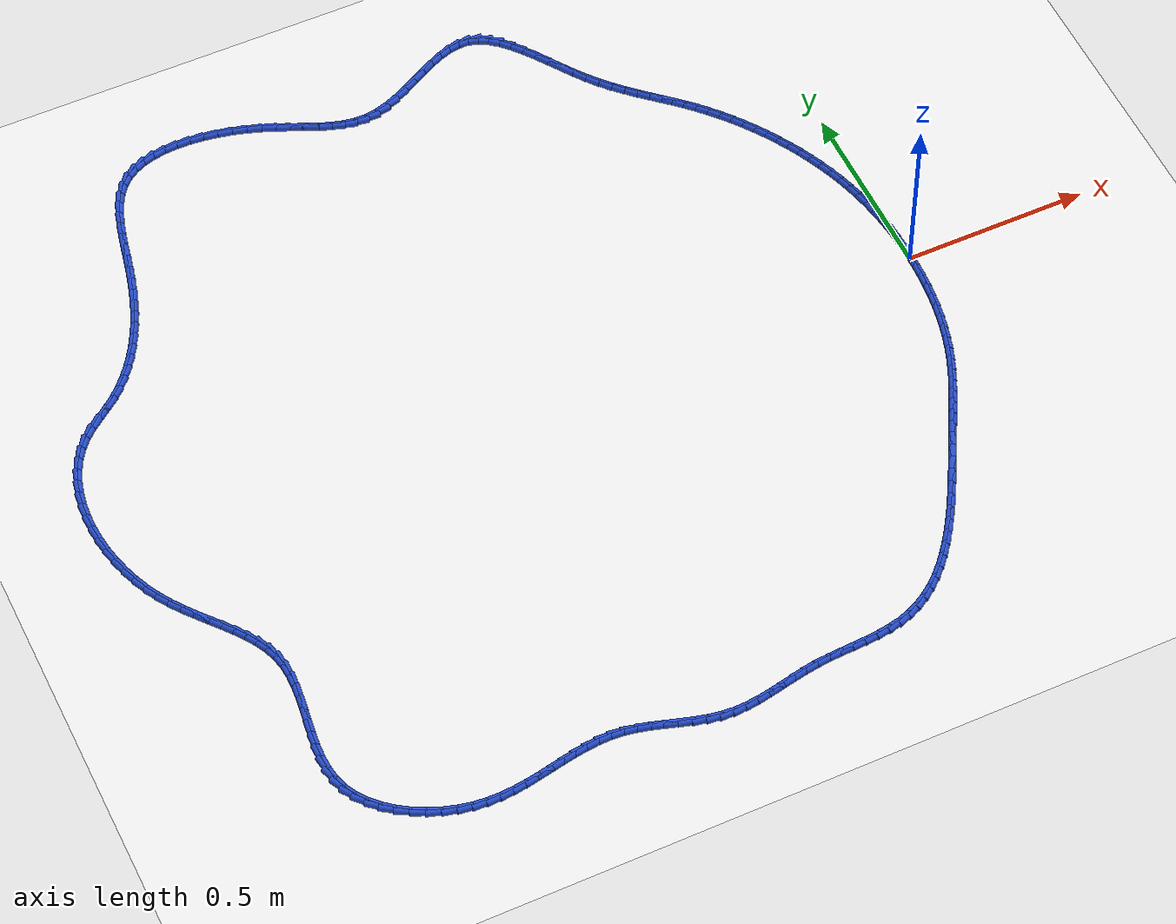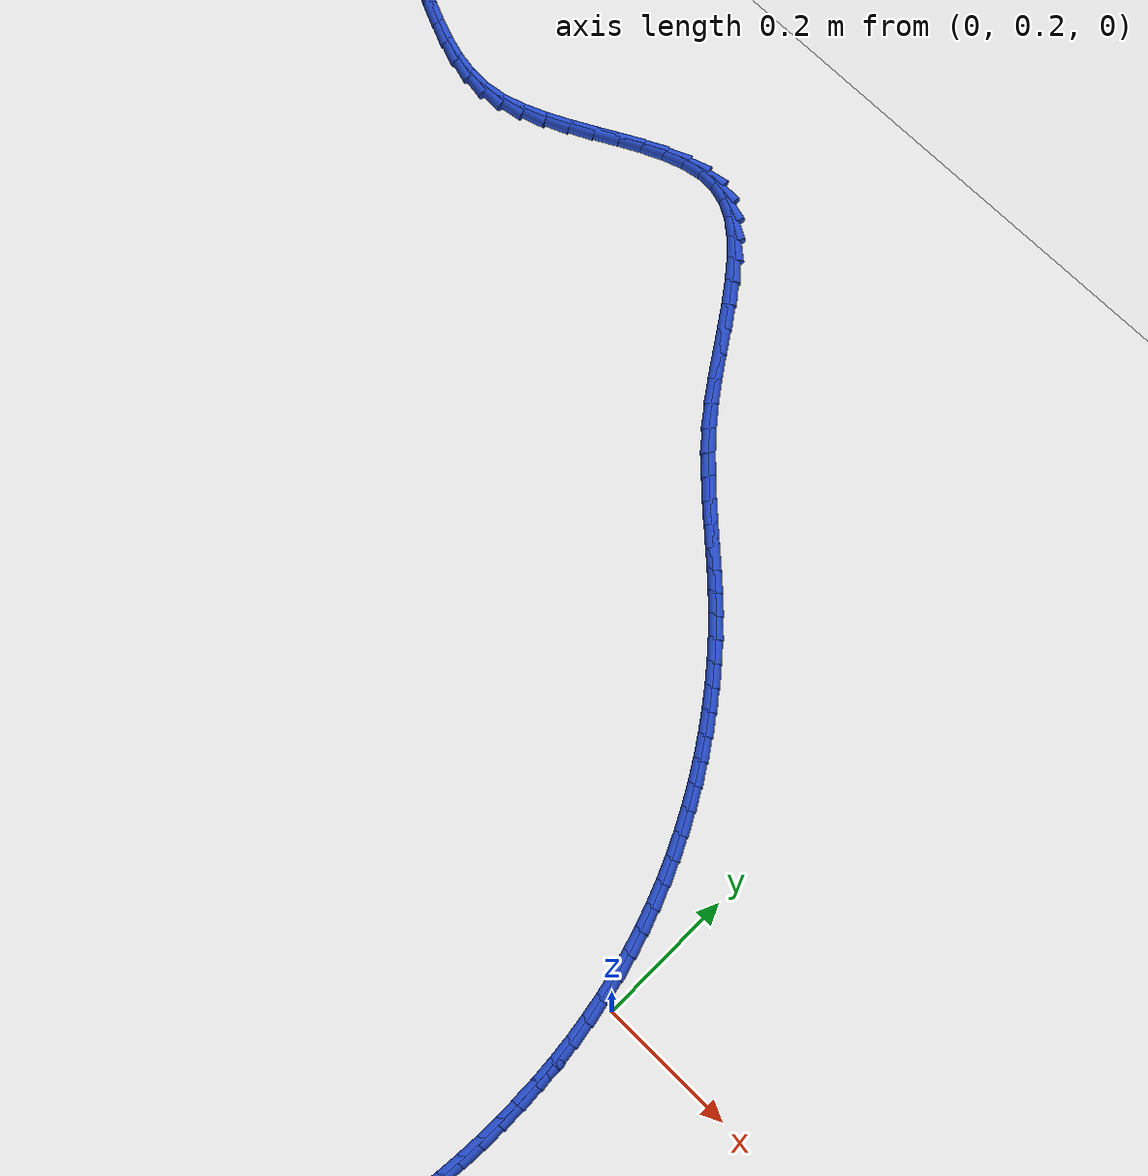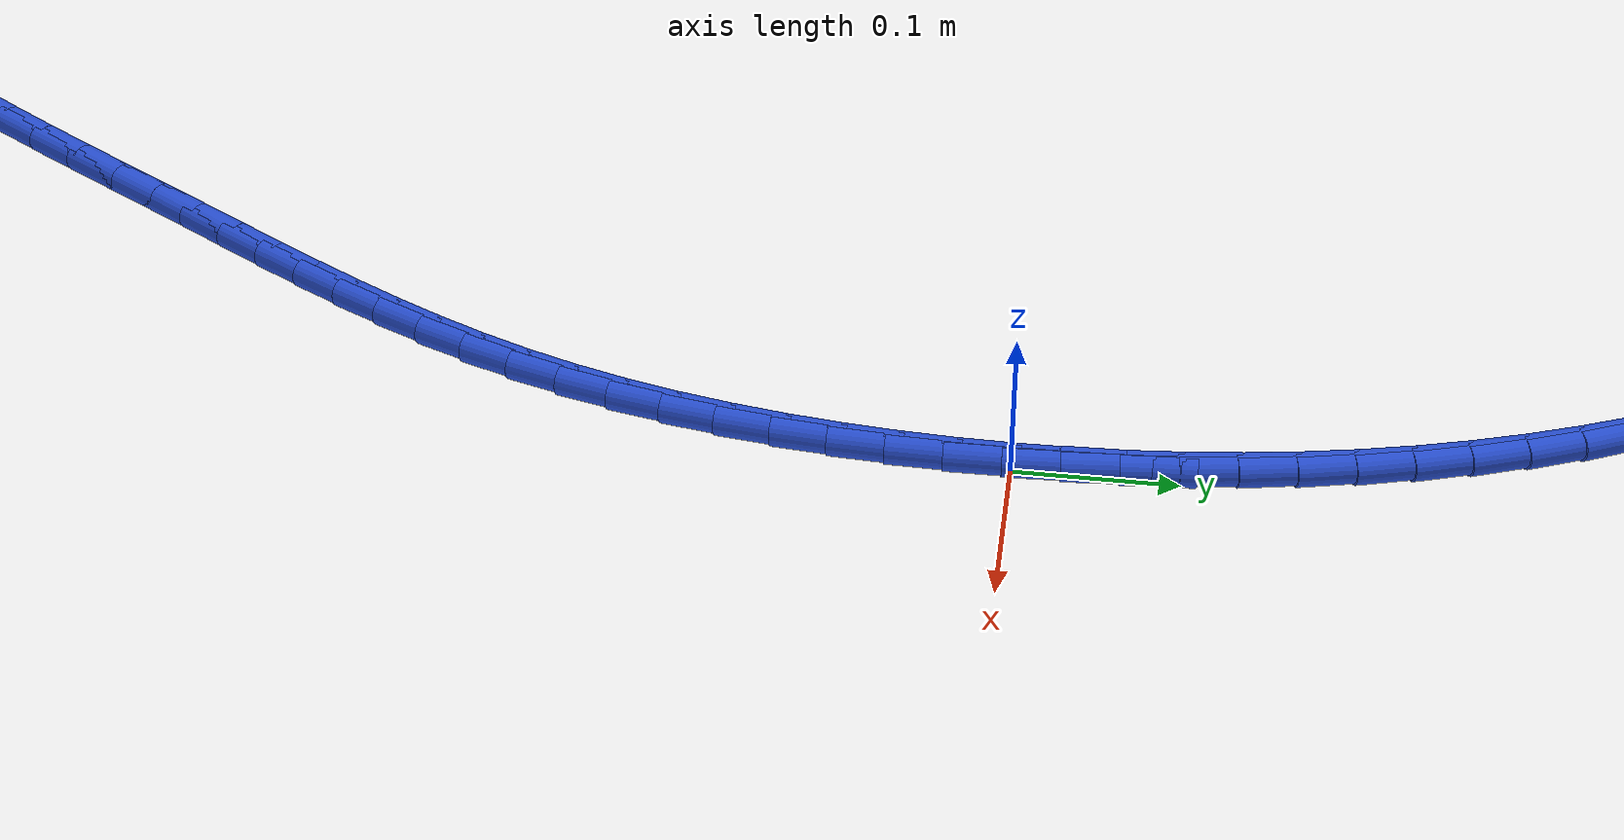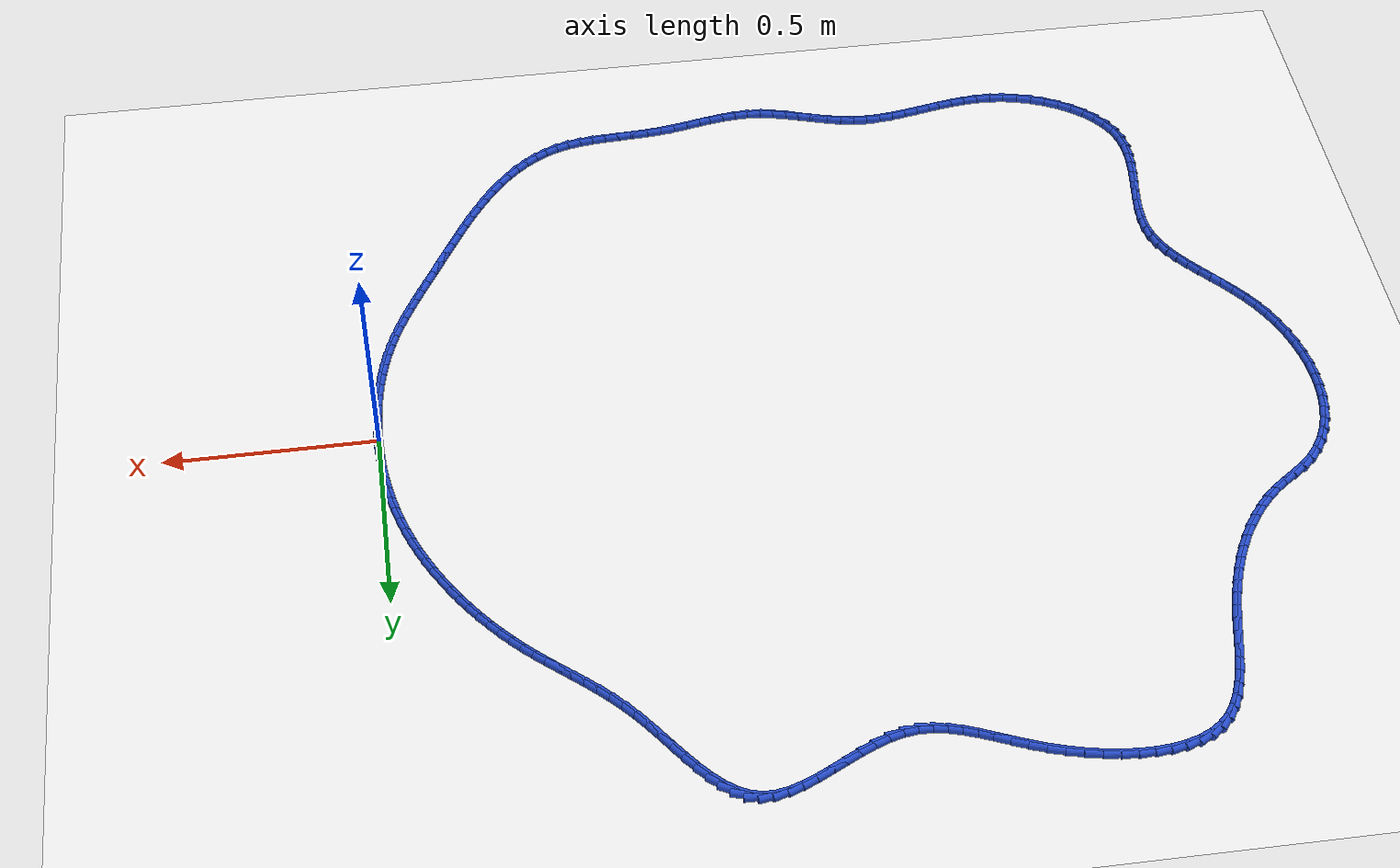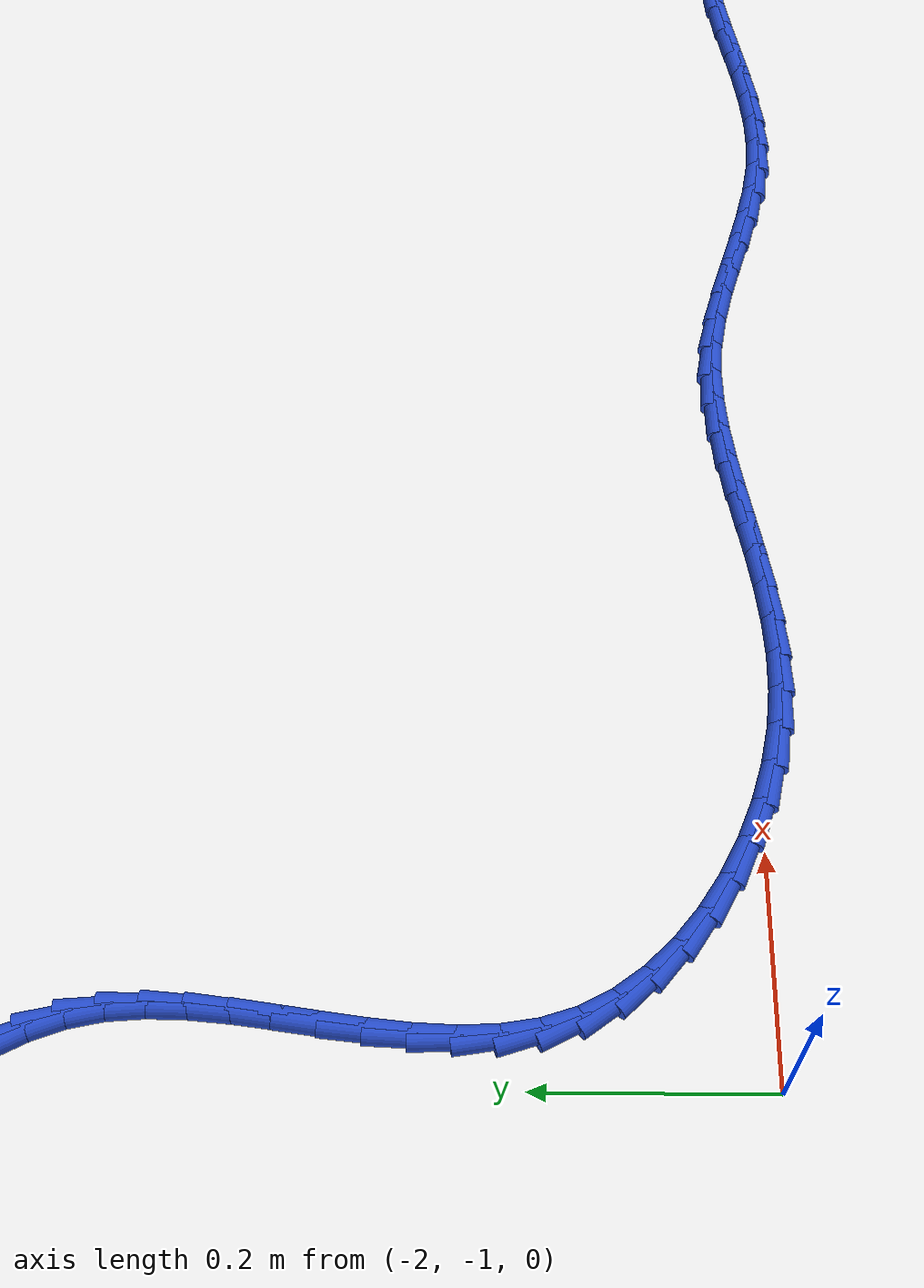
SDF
<sdf version="1.6">
 <world name="default">
  <light name="sun" type="directional">
   <pose>0 0 10 0 -0 0</pose>
   <diffuse>0.8 0.8 0.8 1</diffuse>
   <specular>0.2 0.2 0.2 1</specular>
   <attenuation>
    <range>1000</range>
    <constant>0.9</constant>
    <linear>0.01</linear>
    <quadratic>0.001</quadratic>
   </attenuation>
   <direction>-0.5 0.1 -0.9</direction>
  </light>
  <model name="ground_plane">
   <static>1</static>
   <link name="link">
    <collision name="collision">
     <geometry><plane><normal>0 0 1</normal><size>100 100</size></plane></geometry>
     <surface><friction><ode><mu>100</mu><mu2>50</mu2></ode></friction></surface>
    </collision>
    <visual name="visual">
     <cast_shadows>0</cast_shadows>
     <geometry><plane><normal>0 0 1</normal><size>100 100</size></plane></geometry>
     <material>
      <script><uri>file://media/materials/scripts/gazebo.material</uri><name>Gazebo/WhiteGlow</name></script>
     </material>
    </visual>
   </link>
  </model>
  <gravity>0 0 -9.8</gravity>
  <magnetic_field>6e-06 2.3e-05 -4.2e-05</magnetic_field>
  <atmosphere type="adiabatic"/>
  <physics name="default_physics" default="0" type="ode">
   <max_step_size>0.001</max_step_size>
   <real_time_factor>1</real_time_factor>
   <real_time_update_rate>1000</real_time_update_rate>
  </physics>
  <scene><ambient>0.4 0.4 0.4 1</ambient><background>0.7 0.7 0.7 1</background><shadows>1</shadows></scene>
  <spherical_coordinates>
   <surface_model>EARTH_WGS84</surface_model>
   <latitude_deg>0</latitude_deg>
   <longitude_deg>0</longitude_deg>
   <elevation>0</elevation>
   <heading_deg>0</heading_deg>
  </spherical_coordinates>
  <model name="line">
   <link name="link_0">
    <pose>4.336808689942018e-18 6.245004513516506e-17 0.01 0 1.57 -1.5543038587531324</pose>
    <collision name="collision">
     <geometry><cylinder><radius>0.01</radius><length>0.08</length></cylinder></geometry>
    </collision>
    <visual name="visual">
     <material>
      <script><name>Gazebo/Blue</name><uri>file://media/materials/scripts/gazebo.material</uri></script>
     </material>
     <geometry><cylinder><radius>0.01</radius><length>0.08</length></cylinder></geometry>
    </visual>
   </link>
   <link name="link_1">
    <pose>-0.0005671292059175227 0.034384046314379905 0.01 0 1.57 -1.5221937600335682</pose>
    <collision name="collision">
     <geometry><cylinder><radius>0.01</radius><length>0.08</length></cylinder></geometry>
    </collision>
    <visual name="visual">
     <material>
      <script><name>Gazebo/Blue</name><uri>file://media/materials/scripts/gazebo.material</uri></script>
     </material>
     <geometry><cylinder><radius>0.01</radius><length>0.08</length></cylinder></geometry>
    </visual>
   </link>
   <link name="link_2">
    <pose>-0.002233502790082787 0.06864275692588105 0.01 0 1.57 -1.4890286087418458</pose>
    <collision name="collision">
     <geometry><cylinder><radius>0.01</radius><length>0.08</length></cylinder></geometry>
    </collision>
    <visual name="visual">
     <material>
      <script><name>Gazebo/Blue</name><uri>file://media/materials/scripts/gazebo.material</uri></script>
     </material>
     <geometry><cylinder><radius>0.01</radius><length>0.08</length></cylinder></geometry>
    </visual>
   </link>
   <link name="link_3">
    <pose>-0.005029055808505154 0.10275548487936709 0.01 0 1.57 -1.4548206705582785</pose>
    <collision name="collision">
     <geometry><cylinder><radius>0.01</radius><length>0.08</length></cylinder></geometry>
    </collision>
    <visual name="visual">
     <material>
      <script><name>Gazebo/Blue</name><uri>file://media/materials/scripts/gazebo.material</uri></script>
     </material>
     <geometry><cylinder><radius>0.01</radius><length>0.08</length></cylinder></geometry>
    </visual>
   </link>
   <link name="link_4">
    <pose>-0.008983723317193992 0.13670158321970177 0.01 0 1.57 -1.4195926586835725</pose>
    <collision name="collision">
     <geometry><cylinder><radius>0.01</radius><length>0.08</length></cylinder></geometry>
    </collision>
    <visual name="visual">
     <material>
      <script><name>Gazebo/Blue</name><uri>file://media/materials/scripts/gazebo.material</uri></script>
     </material>
     <geometry><cylinder><radius>0.01</radius><length>0.08</length></cylinder></geometry>
    </visual>
   </link>
   <link name="link_5">
    <pose>-0.014127440372158667 0.17046040499174883 0.01 0 1.57 -1.3833787149878822</pose>
    <collision name="collision">
     <geometry><cylinder><radius>0.01</radius><length>0.08</length></cylinder></geometry>
    </collision>
    <visual name="visual">
     <material>
      <script><name>Gazebo/Blue</name><uri>file://media/materials/scripts/gazebo.material</uri></script>
     </material>
     <geometry><cylinder><radius>0.01</radius><length>0.08</length></cylinder></geometry>
    </visual>
   </link>
   <link name="link_6">
    <pose>-0.020490142029408548 0.2040113032403719 0.01 0 1.57 -1.3462252168017579</pose>
    <collision name="collision">
     <geometry><cylinder><radius>0.01</radius><length>0.08</length></cylinder></geometry>
    </collision>
    <visual name="visual">
     <material>
      <script><name>Gazebo/Blue</name><uri>file://media/materials/scripts/gazebo.material</uri></script>
     </material>
     <geometry><cylinder><radius>0.01</radius><length>0.08</length></cylinder></geometry>
    </visual>
   </link>
   <link name="link_7">
    <pose>-0.028101763344953012 0.2373336310104348 0.01 0 1.57 -1.3081913383421713</pose>
    <collision name="collision">
     <geometry><cylinder><radius>0.01</radius><length>0.08</length></cylinder></geometry>
    </collision>
    <visual name="visual">
     <material>
      <script><name>Gazebo/Blue</name><uri>file://media/materials/scripts/gazebo.material</uri></script>
     </material>
     <geometry><cylinder><radius>0.01</radius><length>0.08</length></cylinder></geometry>
    </visual>
   </link>
   <link name="link_8">
    <pose>-0.03699223937480141 0.2704067413468011 0.01 0 1.57 -1.2693551215662515</pose>
    <collision name="collision">
     <geometry><cylinder><radius>0.01</radius><length>0.08</length></cylinder></geometry>
    </collision>
    <visual name="visual">
     <material>
      <script><name>Gazebo/Blue</name><uri>file://media/materials/scripts/gazebo.material</uri></script>
     </material>
     <geometry><cylinder><radius>0.01</radius><length>0.08</length></cylinder></geometry>
    </visual>
   </link>
   <link name="link_9">
    <pose>-0.047191262276369904 0.30320988008475536 0.01 0 1.57 -1.2304243388916005</pose>
    <collision name="collision">
     <geometry><cylinder><radius>0.01</radius><length>0.08</length></cylinder></geometry>
    </collision>
    <visual name="visual">
     <material>
      <script><name>Gazebo/Blue</name><uri>file://media/materials/scripts/gazebo.material</uri></script>
     </material>
     <geometry><cylinder><radius>0.01</radius><length>0.08</length></cylinder></geometry>
    </visual>
   </link>
   <link name="link_10">
    <pose>-0.0587014843492248 0.3357103583186542 0.01 0 1.57 -1.1925507304561973</pose>
    <collision name="collision">
     <geometry><cylinder><radius>0.01</radius><length>0.08</length></cylinder></geometry>
    </collision>
    <visual name="visual">
     <material>
      <script><name>Gazebo/Blue</name><uri>file://media/materials/scripts/gazebo.material</uri></script>
     </material>
     <geometry><cylinder><radius>0.01</radius><length>0.08</length></cylinder></geometry>
    </visual>
   </link>
   <link name="link_11">
    <pose>-0.07147426167104569 0.3678528462280171 0.01 0 1.57 -1.1557287060929375</pose>
    <collision name="collision">
     <geometry><cylinder><radius>0.01</radius><length>0.08</length></cylinder></geometry>
    </collision>
    <visual name="visual">
     <material>
      <script><name>Gazebo/Blue</name><uri>file://media/materials/scripts/gazebo.material</uri></script>
     </material>
     <geometry><cylinder><radius>0.01</radius><length>0.08</length></cylinder></geometry>
    </visual>
   </link>
   <link name="link_12">
    <pose>-0.08545522337515178 0.3995794862572829 0.01 0 1.57 -1.119813882808674</pose>
    <collision name="collision">
     <geometry><cylinder><radius>0.01</radius><length>0.08</length></cylinder></geometry>
    </collision>
    <visual name="visual">
     <material>
      <script><name>Gazebo/Blue</name><uri>file://media/materials/scripts/gazebo.material</uri></script>
     </material>
     <geometry><cylinder><radius>0.01</radius><length>0.08</length></cylinder></geometry>
    </visual>
   </link>
   <link name="link_13">
    <pose>-0.10058999859486242 0.4308324208508911 0.01 0 1.57 -1.0846611023132795</pose>
    <collision name="collision">
     <geometry><cylinder><radius>0.01</radius><length>0.08</length></cylinder></geometry>
    </collision>
    <visual name="visual">
     <material>
      <script><name>Gazebo/Blue</name><uri>file://media/materials/scripts/gazebo.material</uri></script>
     </material>
     <geometry><cylinder><radius>0.01</radius><length>0.08</length></cylinder></geometry>
    </visual>
   </link>
   <link name="link_14">
    <pose>-0.11682421646349689 0.46155379245328065 0.01 0 1.57 -1.0501246384967802</pose>
    <collision name="collision">
     <geometry><cylinder><radius>0.01</radius><length>0.08</length></cylinder></geometry>
    </collision>
    <visual name="visual">
     <material>
      <script><name>Gazebo/Blue</name><uri>file://media/materials/scripts/gazebo.material</uri></script>
     </material>
     <geometry><cylinder><radius>0.01</radius><length>0.08</length></cylinder></geometry>
    </visual>
   </link>
   <link name="link_15">
    <pose>-0.13410350611437438 0.4916857435088907 0.01 0 1.57 -1.0160580395984238</pose>
    <collision name="collision">
     <geometry><cylinder><radius>0.01</radius><length>0.08</length></cylinder></geometry>
    </collision>
    <visual name="visual">
     <material>
      <script><name>Gazebo/Blue</name><uri>file://media/materials/scripts/gazebo.material</uri></script>
     </material>
     <geometry><cylinder><radius>0.01</radius><length>0.08</length></cylinder></geometry>
    </visual>
   </link>
   <link name="link_16">
    <pose>-0.15237349668081424 0.5211704164621606 0.01 0 1.57 -0.98231366994822</pose>
    <collision name="collision">
     <geometry><cylinder><radius>0.01</radius><length>0.08</length></cylinder></geometry>
    </collision>
    <visual name="visual">
     <material>
      <script><name>Gazebo/Blue</name><uri>file://media/materials/scripts/gazebo.material</uri></script>
     </material>
     <geometry><cylinder><radius>0.01</radius><length>0.08</length></cylinder></geometry>
    </visual>
   </link>
   <link name="link_17">
    <pose>-0.17157981729613575 0.5499499537575293 0.01 0 1.57 -0.9487420032350163</pose>
    <collision name="collision">
     <geometry><cylinder><radius>0.01</radius><length>0.08</length></cylinder></geometry>
    </collision>
    <visual name="visual">
     <material>
      <script><name>Gazebo/Blue</name><uri>file://media/materials/scripts/gazebo.material</uri></script>
     </material>
     <geometry><cylinder><radius>0.01</radius><length>0.08</length></cylinder></geometry>
    </visual>
   </link>
   <link name="link_18">
    <pose>-0.19166809709365823 0.5779664978394363 0.01 0 1.57 -0.9151907084023931</pose>
    <collision name="collision">
     <geometry><cylinder><radius>0.01</radius><length>0.08</length></cylinder></geometry>
    </collision>
    <visual name="visual">
     <material>
      <script><name>Gazebo/Blue</name><uri>file://media/materials/scripts/gazebo.material</uri></script>
     </material>
     <geometry><cylinder><radius>0.01</radius><length>0.08</length></cylinder></geometry>
    </visual>
   </link>
   <link name="link_19">
    <pose>-0.21258396520670086 0.6051621911523204 0.01 0 1.57 -0.8815035611328907</pose>
    <collision name="collision">
     <geometry><cylinder><radius>0.01</radius><length>0.08</length></cylinder></geometry>
    </collision>
    <visual name="visual">
     <material>
      <script><name>Gazebo/Blue</name><uri>file://media/materials/scripts/gazebo.material</uri></script>
     </material>
     <geometry><cylinder><radius>0.01</radius><length>0.08</length></cylinder></geometry>
    </visual>
   </link>
   <link name="link_20">
    <pose>-0.234273050768583 0.631479176140621 0.01 0 1.57 -0.8475192089895005</pose>
    <collision name="collision">
     <geometry><cylinder><radius>0.01</radius><length>0.08</length></cylinder></geometry>
    </collision>
    <visual name="visual">
     <material>
      <script><name>Gazebo/Blue</name><uri>file://media/materials/scripts/gazebo.material</uri></script>
     </material>
     <geometry><cylinder><radius>0.01</radius><length>0.08</length></cylinder></geometry>
    </visual>
   </link>
   <link name="link_21">
    <pose>-0.2566809829126238 0.6568595952487771 0.01 0 1.57 -0.8130698172614506</pose>
    <collision name="collision">
     <geometry><cylinder><radius>0.01</radius><length>0.08</length></cylinder></geometry>
    </collision>
    <visual name="visual">
     <material>
      <script><name>Gazebo/Blue</name><uri>file://media/materials/scripts/gazebo.material</uri></script>
     </material>
     <geometry><cylinder><radius>0.01</radius><length>0.08</length></cylinder></geometry>
    </visual>
   </link>
   <link name="link_22">
    <pose>-0.2797533907721429 0.6812455909212283 0.01 0 1.57 -0.7788516701471598</pose>
    <collision name="collision">
     <geometry><cylinder><radius>0.01</radius><length>0.08</length></cylinder></geometry>
    </collision>
    <visual name="visual">
     <material>
      <script><name>Gazebo/Blue</name><uri>file://media/materials/scripts/gazebo.material</uri></script>
     </material>
     <geometry><cylinder><radius>0.01</radius><length>0.08</length></cylinder></geometry>
    </visual>
   </link>
   <link name="link_23">
    <pose>-0.30342885097133065 0.7046130803685452 0.01 0 1.57 -0.7521788629473859</pose>
    <collision name="collision">
     <geometry><cylinder><radius>0.01</radius><length>0.08</length></cylinder></geometry>
    </collision>
    <visual name="visual">
     <material>
      <script><name>Gazebo/Blue</name><uri>file://media/materials/scripts/gazebo.material</uri></script>
     </material>
     <geometry><cylinder><radius>0.01</radius><length>0.08</length></cylinder></geometry>
    </visual>
   </link>
   <link name="link_24">
    <pose>-0.3275875242645439 0.727217736886143 0.01 0 1.57 -0.7371262131885831</pose>
    <collision name="collision">
     <geometry><cylinder><radius>0.01</radius><length>0.08</length></cylinder></geometry>
    </collision>
    <visual name="visual">
     <material>
      <script><name>Gazebo/Blue</name><uri>file://media/materials/scripts/gazebo.material</uri></script>
     </material>
     <geometry><cylinder><radius>0.01</radius><length>0.08</length></cylinder></geometry>
    </visual>
   </link>
   <link name="link_25">
    <pose>-0.3520807064051882 0.7494534694865063 0.01 0 1.57 -0.7339510638346028</pose>
    <collision name="collision">
     <geometry><cylinder><radius>0.01</radius><length>0.08</length></cylinder></geometry>
    </collision>
    <visual name="visual">
     <material>
      <script><name>Gazebo/Blue</name><uri>file://media/materials/scripts/gazebo.material</uri></script>
     </material>
     <geometry><cylinder><radius>0.01</radius><length>0.08</length></cylinder></geometry>
    </visual>
   </link>
   <link name="link_26">
    <pose>-0.3767594885159683 0.7717151671672501 0.01 0 1.57 -0.7425340094391835</pose>
    <collision name="collision">
     <geometry><cylinder><radius>0.01</radius><length>0.08</length></cylinder></geometry>
    </collision>
    <visual name="visual">
     <material>
      <script><name>Gazebo/Blue</name><uri>file://media/materials/scripts/gazebo.material</uri></script>
     </material>
     <geometry><cylinder><radius>0.01</radius><length>0.08</length></cylinder></geometry>
    </visual>
   </link>
   <link name="link_27">
    <pose>-0.4014749617195892 0.7943977189259896 0.01 0 1.57 -0.7624307895153013</pose>
    <collision name="collision">
     <geometry><cylinder><radius>0.01</radius><length>0.08</length></cylinder></geometry>
    </collision>
    <visual name="visual">
     <material>
      <script><name>Gazebo/Blue</name><uri>file://media/materials/scripts/gazebo.material</uri></script>
     </material>
     <geometry><cylinder><radius>0.01</radius><length>0.08</length></cylinder></geometry>
    </visual>
   </link>
   <link name="link_28">
    <pose>-0.42607821713875554 0.81789601376034 0.01 0 1.57 -0.7928759089515474</pose>
    <collision name="collision">
     <geometry><cylinder><radius>0.01</radius><length>0.08</length></cylinder></geometry>
    </collision>
    <visual name="visual">
     <material>
      <script><name>Gazebo/Blue</name><uri>file://media/materials/scripts/gazebo.material</uri></script>
     </material>
     <geometry><cylinder><radius>0.01</radius><length>0.08</length></cylinder></geometry>
    </visual>
   </link>
   <link name="link_29">
    <pose>-0.45042034589617175 0.8426049406679159 0.01 0 1.57 -0.8327759910491431</pose>
    <collision name="collision">
     <geometry><cylinder><radius>0.01</radius><length>0.08</length></cylinder></geometry>
    </collision>
    <visual name="visual">
     <material>
      <script><name>Gazebo/Blue</name><uri>file://media/materials/scripts/gazebo.material</uri></script>
     </material>
     <geometry><cylinder><radius>0.01</radius><length>0.08</length></cylinder></geometry>
    </visual>
   </link>
   <link name="link_30">
    <pose>-0.474352439114543 0.8689193886463328 0.01 0 1.57 -0.8807145200349252</pose>
    <collision name="collision">
     <geometry><cylinder><radius>0.01</radius><length>0.08</length></cylinder></geometry>
    </collision>
    <visual name="visual">
     <material>
      <script><name>Gazebo/Blue</name><uri>file://media/materials/scripts/gazebo.material</uri></script>
     </material>
     <geometry><cylinder><radius>0.01</radius><length>0.08</length></cylinder></geometry>
    </visual>
   </link>
   <link name="link_31">
    <pose>-0.4977255929850802 0.8972342282198725 0.01 0 1.57 -0.9294383873199956</pose>
    <collision name="collision">
     <geometry><cylinder><radius>0.01</radius><length>0.08</length></cylinder></geometry>
    </collision>
    <visual name="visual">
     <material>
      <script><name>Gazebo/Blue</name><uri>file://media/materials/scripts/gazebo.material</uri></script>
     </material>
     <geometry><cylinder><radius>0.01</radius><length>0.08</length></cylinder></geometry>
    </visual>
   </link>
   <link name="link_32">
    <pose>-0.5204620044180258 0.9276851870653086 0.01 0 1.57 -0.9600022607746695</pose>
    <collision name="collision">
     <geometry><cylinder><radius>0.01</radius><length>0.08</length></cylinder></geometry>
    </collision>
    <visual name="visual">
     <material>
      <script><name>Gazebo/Blue</name><uri>file://media/materials/scripts/gazebo.material</uri></script>
     </material>
     <geometry><cylinder><radius>0.01</radius><length>0.08</length></cylinder></geometry>
    </visual>
   </link>
   <link name="link_33">
    <pose>-0.5427337291826932 0.9594973250476403 0.01 0 1.57 -0.9706734466050098</pose>
    <collision name="collision">
     <geometry><cylinder><radius>0.01</radius><length>0.08</length></cylinder></geometry>
    </collision>
    <visual name="visual">
     <material>
      <script><name>Gazebo/Blue</name><uri>file://media/materials/scripts/gazebo.material</uri></script>
     </material>
     <geometry><cylinder><radius>0.01</radius><length>0.08</length></cylinder></geometry>
    </visual>
   </link>
   <link name="link_34">
    <pose>-0.5647676785250512 0.991695768689198 0.01 0 1.57 -0.9622782402436055</pose>
    <collision name="collision">
     <geometry><cylinder><radius>0.01</radius><length>0.08</length></cylinder></geometry>
    </collision>
    <visual name="visual">
     <material>
      <script><name>Gazebo/Blue</name><uri>file://media/materials/scripts/gazebo.material</uri></script>
     </material>
     <geometry><cylinder><radius>0.01</radius><length>0.08</length></cylinder></geometry>
    </visual>
   </link>
   <link name="link_35">
    <pose>-0.5867907636910692 1.023305644512313 0.01 0 1.57 -0.9336234096131805</pose>
    <collision name="collision">
     <geometry><cylinder><radius>0.01</radius><length>0.08</length></cylinder></geometry>
    </collision>
    <visual name="visual">
     <material>
      <script><name>Gazebo/Blue</name><uri>file://media/materials/scripts/gazebo.material</uri></script>
     </material>
     <geometry><cylinder><radius>0.01</radius><length>0.08</length></cylinder></geometry>
    </visual>
   </link>
   <link name="link_36">
    <pose>-0.6090298959267152 1.053352079039315 0.01 0 1.57 -0.8812582470908706</pose>
    <collision name="collision">
     <geometry><cylinder><radius>0.01</radius><length>0.08</length></cylinder></geometry>
    </collision>
    <visual name="visual">
     <material>
      <script><name>Gazebo/Blue</name><uri>file://media/materials/scripts/gazebo.material</uri></script>
     </material>
     <geometry><cylinder><radius>0.01</radius><length>0.08</length></cylinder></geometry>
    </visual>
   </link>
   <link name="link_37">
    <pose>-0.6317119864779592 1.0808601987925353 0.01 0 1.57 -0.7989773413859008</pose>
    <collision name="collision">
     <geometry><cylinder><radius>0.01</radius><length>0.08</length></cylinder></geometry>
    </collision>
    <visual name="visual">
     <material>
      <script><name>Gazebo/Blue</name><uri>file://media/materials/scripts/gazebo.material</uri></script>
     </material>
     <geometry><cylinder><radius>0.01</radius><length>0.08</length></cylinder></geometry>
    </visual>
   </link>
   <link name="link_38">
    <pose>-0.6550639465907696 1.104855130294304 0.01 0 1.57 -0.6774477252845166</pose>
    <collision name="collision">
     <geometry><cylinder><radius>0.01</radius><length>0.08</length></cylinder></geometry>
    </collision>
    <visual name="visual">
     <material>
      <script><name>Gazebo/Blue</name><uri>file://media/materials/scripts/gazebo.material</uri></script>
     </material>
     <geometry><cylinder><radius>0.01</radius><length>0.08</length></cylinder></geometry>
    </visual>
   </link>
   <link name="link_39">
    <pose>-0.6793126875111155 1.124362000066952 0.01 0 1.57 -0.5055352162435752</pose>
    <collision name="collision">
     <geometry><cylinder><radius>0.01</radius><length>0.08</length></cylinder></geometry>
    </collision>
    <visual name="visual">
     <material>
      <script><name>Gazebo/Blue</name><uri>file://media/materials/scripts/gazebo.material</uri></script>
     </material>
     <geometry><cylinder><radius>0.01</radius><length>0.08</length></cylinder></geometry>
    </visual>
   </link>
   <link name="link_40">
    <pose>-0.704685120484966 1.13840593463281 0.01 0 1.57 -0.2772951215703346</pose>
    <collision name="collision">
     <geometry><cylinder><radius>0.01</radius><length>0.08</length></cylinder></geometry>
    </collision>
    <visual name="visual">
     <material>
      <script><name>Gazebo/Blue</name><uri>file://media/materials/scripts/gazebo.material</uri></script>
     </material>
     <geometry><cylinder><radius>0.01</radius><length>0.08</length></cylinder></geometry>
    </visual>
   </link>
   <link name="link_41">
    <pose>-0.7314081567582897 1.146012060514208 0.01 0 1.57 -0.018709795645509186</pose>
    <collision name="collision">
     <geometry><cylinder><radius>0.01</radius><length>0.08</length></cylinder></geometry>
    </collision>
    <visual name="visual">
     <material>
      <script><name>Gazebo/Blue</name><uri>file://media/materials/scripts/gazebo.material</uri></script>
     </material>
     <geometry><cylinder><radius>0.01</radius><length>0.08</length></cylinder></geometry>
    </visual>
   </link>
   <link name="link_42">
    <pose>-0.7596430529703271 1.14654039130238 0.01 0 1.57 0.18999562240228327</pose>
    <collision name="collision">
     <geometry><cylinder><radius>0.01</radius><length>0.08</length></cylinder></geometry>
    </collision>
    <visual name="visual">
     <material>
      <script><name>Gazebo/Blue</name><uri>file://media/materials/scripts/gazebo.material</uri></script>
     </material>
     <geometry><cylinder><radius>0.01</radius><length>0.08</length></cylinder></geometry>
    </visual>
   </link>
   <link name="link_43">
    <pose>-0.7892581647887804 1.1408449522462987 0.01 0 1.57 0.3330526460474649</pose>
    <collision name="collision">
     <geometry><cylinder><radius>0.01</radius><length>0.08</length></cylinder></geometry>
    </collision>
    <visual name="visual">
     <material>
      <script><name>Gazebo/Blue</name><uri>file://media/materials/scripts/gazebo.material</uri></script>
     </material>
     <geometry><cylinder><radius>0.01</radius><length>0.08</length></cylinder></geometry>
    </visual>
   </link>
   <link name="link_44">
    <pose>-0.8200401989148011 1.1301962387323627 0.01 0 1.57 0.4241745491738958</pose>
    <collision name="collision">
     <geometry><cylinder><radius>0.01</radius><length>0.08</length></cylinder></geometry>
    </collision>
    <visual name="visual">
     <material>
      <script><name>Gazebo/Blue</name><uri>file://media/materials/scripts/gazebo.material</uri></script>
     </material>
     <geometry><cylinder><radius>0.01</radius><length>0.08</length></cylinder></geometry>
    </visual>
   </link>
   <link name="link_45">
    <pose>-0.8517758585257734 1.1158647641207946 0.01 0 1.57 0.47602775585244717</pose>
    <collision name="collision">
     <geometry><cylinder><radius>0.01</radius><length>0.08</length></cylinder></geometry>
    </collision>
    <visual name="visual">
     <material>
      <script><name>Gazebo/Blue</name><uri>file://media/materials/scripts/gazebo.material</uri></script>
     </material>
     <geometry><cylinder><radius>0.01</radius><length>0.08</length></cylinder></geometry>
    </visual>
   </link>
   <link name="link_46">
    <pose>-0.8842518467990811 1.099121041771816 0.01 0 1.57 0.4966293739215362</pose>
    <collision name="collision">
     <geometry><cylinder><radius>0.01</radius><length>0.08</length></cylinder></geometry>
    </collision>
    <visual name="visual">
     <material>
      <script><name>Gazebo/Blue</name><uri>file://media/materials/scripts/gazebo.material</uri></script>
     </material>
     <geometry><cylinder><radius>0.01</radius><length>0.08</length></cylinder></geometry>
    </visual>
   </link>
   <link name="link_47">
    <pose>-0.9172548669121082 1.0812355850456496 0.01 0 1.57 0.4896708296371982</pose>
    <collision name="collision">
     <geometry><cylinder><radius>0.01</radius><length>0.08</length></cylinder></geometry>
    </collision>
    <visual name="visual">
     <material>
      <script><name>Gazebo/Blue</name><uri>file://media/materials/scripts/gazebo.material</uri></script>
     </material>
     <geometry><cylinder><radius>0.01</radius><length>0.08</length></cylinder></geometry>
    </visual>
   </link>
   <link name="link_48">
    <pose>-0.9505716220422389 1.0634789073025175 0.01 0 1.57 0.45520439621556347</pose>
    <collision name="collision">
     <geometry><cylinder><radius>0.01</radius><length>0.08</length></cylinder></geometry>
    </collision>
    <visual name="visual">
     <material>
      <script><name>Gazebo/Blue</name><uri>file://media/materials/scripts/gazebo.material</uri></script>
     </material>
     <geometry><cylinder><radius>0.01</radius><length>0.08</length></cylinder></geometry>
    </visual>
   </link>
   <link name="link_49">
    <pose>-0.9839888153668571 1.0471215219026417 0.01 0 1.57 0.3899401300883945</pose>
    <collision name="collision">
     <geometry><cylinder><radius>0.01</radius><length>0.08</length></cylinder></geometry>
    </collision>
    <visual name="visual">
     <material>
      <script><name>Gazebo/Blue</name><uri>file://media/materials/scripts/gazebo.material</uri></script>
     </material>
     <geometry><cylinder><radius>0.01</radius><length>0.08</length></cylinder></geometry>
    </visual>
   </link>
   <link name="link_50">
    <pose>-1.0172931500633462 1.0334339422062448 0.01 0 1.57 0.28738485203527775</pose>
    <collision name="collision">
     <geometry><cylinder><radius>0.01</radius><length>0.08</length></cylinder></geometry>
    </collision>
    <visual name="visual">
     <material>
      <script><name>Gazebo/Blue</name><uri>file://media/materials/scripts/gazebo.material</uri></script>
     </material>
     <geometry><cylinder><radius>0.01</radius><length>0.08</length></cylinder></geometry>
    </visual>
   </link>
   <link name="link_51">
    <pose>-1.0502713293090908 1.0236866815735488 0.01 0 1.57 0.13985838433105413</pose>
    <collision name="collision">
     <geometry><cylinder><radius>0.01</radius><length>0.08</length></cylinder></geometry>
    </collision>
    <visual name="visual">
     <material>
      <script><name>Gazebo/Blue</name><uri>file://media/materials/scripts/gazebo.material</uri></script>
     </material>
     <geometry><cylinder><radius>0.01</radius><length>0.08</length></cylinder></geometry>
    </visual>
   </link>
   <link name="link_52">
    <pose>-1.082716747532836 1.0191190976871956 0.01 0 1.57 -0.027836465849046955</pose>
    <collision name="collision">
     <geometry><cylinder><radius>0.01</radius><length>0.08</length></cylinder></geometry>
    </collision>
    <visual name="visual">
     <material>
      <script><name>Gazebo/Blue</name><uri>file://media/materials/scripts/gazebo.material</uri></script>
     </material>
     <geometry><cylinder><radius>0.01</radius><length>0.08</length></cylinder></geometry>
    </visual>
   </link>
   <link name="link_53">
    <pose>-1.1146295952741725 1.0200076681038566 0.01 0 1.57 -0.172135095002909</pose>
    <collision name="collision">
     <geometry><cylinder><radius>0.01</radius><length>0.08</length></cylinder></geometry>
    </collision>
    <visual name="visual">
     <material>
      <script><name>Gazebo/Blue</name><uri>file://media/materials/scripts/gazebo.material</uri></script>
     </material>
     <geometry><cylinder><radius>0.01</radius><length>0.08</length></cylinder></geometry>
    </visual>
   </link>
   <link name="link_54">
    <pose>-1.146251372004763 1.0255052923111299 0.01 0 1.57 -0.28331267687313844</pose>
    <collision name="collision">
     <geometry><cylinder><radius>0.01</radius><length>0.08</length></cylinder></geometry>
    </collision>
    <visual name="visual">
     <material>
      <script><name>Gazebo/Blue</name><uri>file://media/materials/scripts/gazebo.material</uri></script>
     </material>
     <geometry><cylinder><radius>0.01</radius><length>0.08</length></cylinder></geometry>
    </visual>
   </link>
   <link name="link_55">
    <pose>-1.1778372225994858 1.0347013343291769 0.01 0 1.57 -0.36033883460108596</pose>
    <collision name="collision">
     <geometry><cylinder><radius>0.01</radius><length>0.08</length></cylinder></geometry>
    </collision>
    <visual name="visual">
     <material>
      <script><name>Gazebo/Blue</name><uri>file://media/materials/scripts/gazebo.material</uri></script>
     </material>
     <geometry><cylinder><radius>0.01</radius><length>0.08</length></cylinder></geometry>
    </visual>
   </link>
   <link name="link_56">
    <pose>-1.2096422919332206 1.0466851581781602 0.01 0 1.57 -0.4055963156021776</pose>
    <collision name="collision">
     <geometry><cylinder><radius>0.01</radius><length>0.08</length></cylinder></geometry>
    </collision>
    <visual name="visual">
     <material>
      <script><name>Gazebo/Blue</name><uri>file://media/materials/scripts/gazebo.material</uri></script>
     </material>
     <geometry><cylinder><radius>0.01</radius><length>0.08</length></cylinder></geometry>
    </visual>
   </link>
   <link name="link_57">
    <pose>-1.2419217248808445 1.0605461278782409 0.01 0 1.57 -0.422184994766495</pose>
    <collision name="collision">
     <geometry><cylinder><radius>0.01</radius><length>0.08</length></cylinder></geometry>
    </collision>
    <visual name="visual">
     <material>
      <script><name>Gazebo/Blue</name><uri>file://media/materials/scripts/gazebo.material</uri></script>
     </material>
     <geometry><cylinder><radius>0.01</radius><length>0.08</length></cylinder></geometry>
    </visual>
   </link>
   <link name="link_58">
    <pose>-1.2749306663172373 1.0753736074495817 0.01 0 1.57 -0.4126858574819426</pose>
    <collision name="collision">
     <geometry><cylinder><radius>0.01</radius><length>0.08</length></cylinder></geometry>
    </collision>
    <visual name="visual">
     <material>
      <script><name>Gazebo/Blue</name><uri>file://media/materials/scripts/gazebo.material</uri></script>
     </material>
     <geometry><cylinder><radius>0.01</radius><length>0.08</length></cylinder></geometry>
    </visual>
   </link>
   <link name="link_59">
    <pose>-1.3089242611172764 1.090256960912344 0.01 0 1.57 -0.37892236059137874</pose>
    <collision name="collision">
     <geometry><cylinder><radius>0.01</radius><length>0.08</length></cylinder></geometry>
    </collision>
    <visual name="visual">
     <material>
      <script><name>Gazebo/Blue</name><uri>file://media/materials/scripts/gazebo.material</uri></script>
     </material>
     <geometry><cylinder><radius>0.01</radius><length>0.08</length></cylinder></geometry>
    </visual>
   </link>
   <link name="link_60">
    <pose>-1.344157604235979 1.104285599270153 0.01 0 1.57 -0.32696385369625136</pose>
    <collision name="collision">
     <geometry><cylinder><radius>0.01</radius><length>0.08</length></cylinder></geometry>
    </collision>
    <visual name="visual">
     <material>
      <script><name>Gazebo/Blue</name><uri>file://media/materials/scripts/gazebo.material</uri></script>
     </material>
     <geometry><cylinder><radius>0.01</radius><length>0.08</length></cylinder></geometry>
    </visual>
   </link>
   <link name="link_61">
    <pose>-1.3807354236881495 1.116690455540456 0.01 0 1.57 -0.2718424058874159</pose>
    <collision name="collision">
     <geometry><cylinder><radius>0.01</radius><length>0.08</length></cylinder></geometry>
    </collision>
    <visual name="visual">
     <material>
      <script><name>Gazebo/Blue</name><uri>file://media/materials/scripts/gazebo.material</uri></script>
     </material>
     <geometry><cylinder><radius>0.01</radius><length>0.08</length></cylinder></geometry>
    </visual>
   </link>
   <link name="link_62">
    <pose>-1.4182806560998003 1.127155914061116 0.01 0 1.57 -0.21485546204883496</pose>
    <collision name="collision">
     <geometry><cylinder><radius>0.01</radius><length>0.08</length></cylinder></geometry>
    </collision>
    <visual name="visual">
     <material>
      <script><name>Gazebo/Blue</name><uri>file://media/materials/scripts/gazebo.material</uri></script>
     </material>
     <geometry><cylinder><radius>0.01</radius><length>0.08</length></cylinder></geometry>
    </visual>
   </link>
   <link name="link_63">
    <pose>-1.4563199418411725 1.1354569910603662 0.01 0 1.57 -0.15409482429747445</pose>
    <collision name="collision">
     <geometry><cylinder><radius>0.01</radius><length>0.08</length></cylinder></geometry>
    </collision>
    <visual name="visual">
     <material>
      <script><name>Gazebo/Blue</name><uri>file://media/materials/scripts/gazebo.material</uri></script>
     </material>
     <geometry><cylinder><radius>0.01</radius><length>0.08</length></cylinder></geometry>
    </visual>
   </link>
   <link name="link_64">
    <pose>-1.4943799212825049 1.1413687027664399 0.01 0 1.57 -0.08745511263471947</pose>
    <collision name="collision">
     <geometry><cylinder><radius>0.01</radius><length>0.08</length></cylinder></geometry>
    </collision>
    <visual name="visual">
     <material>
      <script><name>Gazebo/Blue</name><uri>file://media/materials/scripts/gazebo.material</uri></script>
     </material>
     <geometry><cylinder><radius>0.01</radius><length>0.08</length></cylinder></geometry>
    </visual>
   </link>
   <link name="link_65">
    <pose>-1.5319872347940378 1.1446660654075707 0.01 0 1.57 -0.01248609378448818</pose>
    <collision name="collision">
     <geometry><cylinder><radius>0.01</radius><length>0.08</length></cylinder></geometry>
    </collision>
    <visual name="visual">
     <material>
      <script><name>Gazebo/Blue</name><uri>file://media/materials/scripts/gazebo.material</uri></script>
     </material>
     <geometry><cylinder><radius>0.01</radius><length>0.08</length></cylinder></geometry>
    </visual>
   </link>
   <link name="link_66">
    <pose>-1.5686685227460118 1.1451240952119919 0.01 0 1.57 0.07373643068246821</pose>
    <collision name="collision">
     <geometry><cylinder><radius>0.01</radius><length>0.08</length></cylinder></geometry>
    </collision>
    <visual name="visual">
     <material>
      <script><name>Gazebo/Blue</name><uri>file://media/materials/scripts/gazebo.material</uri></script>
     </material>
     <geometry><cylinder><radius>0.01</radius><length>0.08</length></cylinder></geometry>
    </visual>
   </link>
   <link name="link_67">
    <pose>-1.6039504255086665 1.1425178084079373 0.01 0 1.57 0.17466794436842395</pose>
    <collision name="collision">
     <geometry><cylinder><radius>0.01</radius><length>0.08</length></cylinder></geometry>
    </collision>
    <visual name="visual">
     <material>
      <script><name>Gazebo/Blue</name><uri>file://media/materials/scripts/gazebo.material</uri></script>
     </material>
     <geometry><cylinder><radius>0.01</radius><length>0.08</length></cylinder></geometry>
    </visual>
   </link>
   <link name="link_68">
    <pose>-1.637359583452242 1.1366222212236399 0.01 0 1.57 0.2941409421928584</pose>
    <collision name="collision">
     <geometry><cylinder><radius>0.01</radius><length>0.08</length></cylinder></geometry>
    </collision>
    <visual name="visual">
     <material>
      <script><name>Gazebo/Blue</name><uri>file://media/materials/scripts/gazebo.material</uri></script>
     </material>
     <geometry><cylinder><radius>0.01</radius><length>0.08</length></cylinder></geometry>
    </visual>
   </link>
   <link name="link_69">
    <pose>-1.6684226369469783 1.127212349887333 0.01 0 1.57 0.4357195800863377</pose>
    <collision name="collision">
     <geometry><cylinder><radius>0.01</radius><length>0.08</length></cylinder></geometry>
    </collision>
    <visual name="visual">
     <material>
      <script><name>Gazebo/Blue</name><uri>file://media/materials/scripts/gazebo.material</uri></script>
     </material>
     <geometry><cylinder><radius>0.01</radius><length>0.08</length></cylinder></geometry>
    </visual>
   </link>
   <link name="link_70">
    <pose>-1.6966662263631158 1.1140632106272508 0.01 0 1.57 0.6011908157689687</pose>
    <collision name="collision">
     <geometry><cylinder><radius>0.01</radius><length>0.08</length></cylinder></geometry>
    </collision>
    <visual name="visual">
     <material>
      <script><name>Gazebo/Blue</name><uri>file://media/materials/scripts/gazebo.material</uri></script>
     </material>
     <geometry><cylinder><radius>0.01</radius><length>0.08</length></cylinder></geometry>
    </visual>
   </link>
   <link name="link_71">
    <pose>-1.721616992070894 1.0969498196716259 0.01 0 1.57 0.7850406480658003</pose>
    <collision name="collision">
     <geometry><cylinder><radius>0.01</radius><length>0.08</length></cylinder></geometry>
    </collision>
    <visual name="visual">
     <material>
      <script><name>Gazebo/Blue</name><uri>file://media/materials/scripts/gazebo.material</uri></script>
     </material>
     <geometry><cylinder><radius>0.01</radius><length>0.08</length></cylinder></geometry>
    </visual>
   </link>
   <link name="link_72">
    <pose>-1.7428768564190924 1.0757051513461702 0.01 0 1.57 0.9536490892849643</pose>
    <collision name="collision">
     <geometry><cylinder><radius>0.01</radius><length>0.08</length></cylinder></geometry>
    </collision>
    <visual name="visual">
     <material>
      <script><name>Gazebo/Blue</name><uri>file://media/materials/scripts/gazebo.material</uri></script>
     </material>
     <geometry><cylinder><radius>0.01</radius><length>0.08</length></cylinder></geometry>
    </visual>
   </link>
   <link name="link_73">
    <pose>-1.7606651377071614 1.0506375008353988 0.01 0 1.57 1.0885914494220699</pose>
    <collision name="collision">
     <geometry><cylinder><radius>0.01</radius><length>0.08</length></cylinder></geometry>
    </collision>
    <visual name="visual">
     <material>
      <script><name>Gazebo/Blue</name><uri>file://media/materials/scripts/gazebo.material</uri></script>
     </material>
     <geometry><cylinder><radius>0.01</radius><length>0.08</length></cylinder></geometry>
    </visual>
   </link>
   <link name="link_74">
    <pose>-1.7755036927709775 1.0222880817237585 0.01 0 1.57 1.1909164609186258</pose>
    <collision name="collision">
     <geometry><cylinder><radius>0.01</radius><length>0.08</length></cylinder></geometry>
    </collision>
    <visual name="visual">
     <material>
      <script><name>Gazebo/Blue</name><uri>file://media/materials/scripts/gazebo.material</uri></script>
     </material>
     <geometry><cylinder><radius>0.01</radius><length>0.08</length></cylinder></geometry>
    </visual>
   </link>
   <link name="link_75">
    <pose>-1.7879164550227946 0.9911997063105349 0.01 0 1.57 1.2649174011875994</pose>
    <collision name="collision">
     <geometry><cylinder><radius>0.01</radius><length>0.08</length></cylinder></geometry>
    </collision>
    <visual name="visual">
     <material>
      <script><name>Gazebo/Blue</name><uri>file://media/materials/scripts/gazebo.material</uri></script>
     </material>
     <geometry><cylinder><radius>0.01</radius><length>0.08</length></cylinder></geometry>
    </visual>
   </link>
   <link name="link_76">
    <pose>-1.7984273578748673 0.9579151868950121 0.01 0 1.57 1.315111400061034</pose>
    <collision name="collision">
     <geometry><cylinder><radius>0.01</radius><length>0.08</length></cylinder></geometry>
    </collision>
    <visual name="visual">
     <material>
      <script><name>Gazebo/Blue</name><uri>file://media/materials/scripts/gazebo.material</uri></script>
     </material>
     <geometry><cylinder><radius>0.01</radius><length>0.08</length></cylinder></geometry>
    </visual>
   </link>
   <link name="link_77">
    <pose>-1.8075603347394487 0.9229773357764767 0.01 0 1.57 1.3450478365298546</pose>
    <collision name="collision">
     <geometry><cylinder><radius>0.01</radius><length>0.08</length></cylinder></geometry>
    </collision>
    <visual name="visual">
     <material>
      <script><name>Gazebo/Blue</name><uri>file://media/materials/scripts/gazebo.material</uri></script>
     </material>
     <geometry><cylinder><radius>0.01</radius><length>0.08</length></cylinder></geometry>
    </visual>
   </link>
   <link name="link_78">
    <pose>-1.8158393190287943 0.8869289652542129 0.01 0 1.57 1.3570249119139484</pose>
    <collision name="collision">
     <geometry><cylinder><radius>0.01</radius><length>0.08</length></cylinder></geometry>
    </collision>
    <visual name="visual">
     <material>
      <script><name>Gazebo/Blue</name><uri>file://media/materials/scripts/gazebo.material</uri></script>
     </material>
     <geometry><cylinder><radius>0.01</radius><length>0.08</length></cylinder></geometry>
    </visual>
   </link>
   <link name="link_79">
    <pose>-1.8237882441551565 0.8503128876275055 0.01 0 1.57 1.3521179907283998</pose>
    <collision name="collision">
     <geometry><cylinder><radius>0.01</radius><length>0.08</length></cylinder></geometry>
    </collision>
    <visual name="visual">
     <material>
      <script><name>Gazebo/Blue</name><uri>file://media/materials/scripts/gazebo.material</uri></script>
     </material>
     <geometry><cylinder><radius>0.01</radius><length>0.08</length></cylinder></geometry>
    </visual>
   </link>
   <link name="link_80">
    <pose>-1.8319310435307916 0.813671915195641 0.01 0 1.57 1.3308188101149714</pose>
    <collision name="collision">
     <geometry><cylinder><radius>0.01</radius><length>0.08</length></cylinder></geometry>
    </collision>
    <visual name="visual">
     <material>
      <script><name>Gazebo/Blue</name><uri>file://media/materials/scripts/gazebo.material</uri></script>
     </material>
     <geometry><cylinder><radius>0.01</radius><length>0.08</length></cylinder></geometry>
    </visual>
   </link>
   <link name="link_81">
    <pose>-1.8407745361681223 0.7775307210288828 0.01 0 1.57 1.3002278407176653</pose>
    <collision name="collision">
     <geometry><cylinder><radius>0.01</radius><length>0.08</length></cylinder></geometry>
    </collision>
    <visual name="visual">
     <material>
      <script><name>Gazebo/Blue</name><uri>file://media/materials/scripts/gazebo.material</uri></script>
     </material>
     <geometry><cylinder><radius>0.01</radius><length>0.08</length></cylinder></geometry>
    </visual>
   </link>
   <link name="link_82">
    <pose>-1.850585456312026 0.7421595168885219 0.01 0 1.57 1.2657732977569667</pose>
    <collision name="collision">
     <geometry><cylinder><radius>0.01</radius><length>0.08</length></cylinder></geometry>
    </collision>
    <visual name="visual">
     <material>
      <script><name>Gazebo/Blue</name><uri>file://media/materials/scripts/gazebo.material</uri></script>
     </material>
     <geometry><cylinder><radius>0.01</radius><length>0.08</length></cylinder></geometry>
    </visual>
   </link>
   <link name="link_83">
    <pose>-1.8614535751484085 0.7076409547331804 0.01 0 1.57 1.2273662343875011</pose>
    <collision name="collision">
     <geometry><cylinder><radius>0.01</radius><length>0.08</length></cylinder></geometry>
    </collision>
    <visual name="visual">
     <material>
      <script><name>Gazebo/Blue</name><uri>file://media/materials/scripts/gazebo.material</uri></script>
     </material>
     <geometry><cylinder><radius>0.01</radius><length>0.08</length></cylinder></geometry>
    </visual>
   </link>
   <link name="link_84">
    <pose>-1.8734645432204677 0.6740533191301273 0.01 0 1.57 1.1847955524513125</pose>
    <collision name="collision">
     <geometry><cylinder><radius>0.01</radius><length>0.08</length></cylinder></geometry>
    </collision>
    <visual name="visual">
     <material>
      <script><name>Gazebo/Blue</name><uri>file://media/materials/scripts/gazebo.material</uri></script>
     </material>
     <geometry><cylinder><radius>0.01</radius><length>0.08</length></cylinder></geometry>
    </visual>
   </link>
   <link name="link_85">
    <pose>-1.8867040110714004 0.6414748946466312 0.01 0 1.57 1.1378822868149392</pose>
    <collision name="collision">
     <geometry><cylinder><radius>0.01</radius><length>0.08</length></cylinder></geometry>
    </collision>
    <visual name="visual">
     <material>
      <script><name>Gazebo/Blue</name><uri>file://media/materials/scripts/gazebo.material</uri></script>
     </material>
     <geometry><cylinder><radius>0.01</radius><length>0.08</length></cylinder></geometry>
    </visual>
   </link>
   <link name="link_86">
    <pose>-1.9012576292444046 0.6099839658499623 0.01 0 1.57 1.0865039645212868</pose>
    <collision name="collision">
     <geometry><cylinder><radius>0.01</radius><length>0.08</length></cylinder></geometry>
    </collision>
    <visual name="visual">
     <material>
      <script><name>Gazebo/Blue</name><uri>file://media/materials/scripts/gazebo.material</uri></script>
     </material>
     <geometry><cylinder><radius>0.01</radius><length>0.08</length></cylinder></geometry>
    </visual>
   </link>
   <link name="link_87">
    <pose>-1.9172110482826765 0.5796588173073889 0.01 0 1.57 1.0306241380098038</pose>
    <collision name="collision">
     <geometry><cylinder><radius>0.01</radius><length>0.08</length></cylinder></geometry>
    </collision>
    <visual name="visual">
     <material>
      <script><name>Gazebo/Blue</name><uri>file://media/materials/scripts/gazebo.material</uri></script>
     </material>
     <geometry><cylinder><radius>0.01</radius><length>0.08</length></cylinder></geometry>
    </visual>
   </link>
   <link name="link_88">
    <pose>-1.9346499187294144 0.55057773358618 0.01 0 1.57 0.9703253128235724</pose>
    <collision name="collision">
     <geometry><cylinder><radius>0.01</radius><length>0.08</length></cylinder></geometry>
    </collision>
    <visual name="visual">
     <material>
      <script><name>Gazebo/Blue</name><uri>file://media/materials/scripts/gazebo.material</uri></script>
     </material>
     <geometry><cylinder><radius>0.01</radius><length>0.08</length></cylinder></geometry>
    </visual>
   </link>
   <link name="link_89">
    <pose>-1.953659891127815 0.5228189992536054 0.01 0 1.57 0.9058415240413282</pose>
    <collision name="collision">
     <geometry><cylinder><radius>0.01</radius><length>0.08</length></cylinder></geometry>
    </collision>
    <visual name="visual">
     <material>
      <script><name>Gazebo/Blue</name><uri>file://media/materials/scripts/gazebo.material</uri></script>
     </material>
     <geometry><cylinder><radius>0.01</radius><length>0.08</length></cylinder></geometry>
    </visual>
   </link>
   <link name="link_90">
    <pose>-1.9743266160210764 0.496460898876934 0.01 0 1.57 0.8375846590928235</pose>
    <collision name="collision">
     <geometry><cylinder><radius>0.01</radius><length>0.08</length></cylinder></geometry>
    </collision>
    <visual name="visual">
     <material>
      <script><name>Gazebo/Blue</name><uri>file://media/materials/scripts/gazebo.material</uri></script>
     </material>
     <geometry><cylinder><radius>0.01</radius><length>0.08</length></cylinder></geometry>
    </visual>
   </link>
   <link name="link_91">
    <pose>-1.9967357439523943 0.47158171702343454 0.01 0 1.57 0.7661570792506457</pose>
    <collision name="collision">
     <geometry><cylinder><radius>0.01</radius><length>0.08</length></cylinder></geometry>
    </collision>
    <visual name="visual">
     <material>
      <script><name>Gazebo/Blue</name><uri>file://media/materials/scripts/gazebo.material</uri></script>
     </material>
     <geometry><cylinder><radius>0.01</radius><length>0.08</length></cylinder></geometry>
    </visual>
   </link>
   <link name="link_92">
    <pose>-2.0209729254649678 0.44825973826037635 0.01 0 1.57 0.6932432770063294</pose>
    <collision name="collision">
     <geometry><cylinder><radius>0.01</radius><length>0.08</length></cylinder></geometry>
    </collision>
    <visual name="visual">
     <material>
      <script><name>Gazebo/Blue</name><uri>file://media/materials/scripts/gazebo.material</uri></script>
     </material>
     <geometry><cylinder><radius>0.01</radius><length>0.08</length></cylinder></geometry>
    </visual>
   </link>
   <link name="link_93">
    <pose>-2.0471004897396075 0.42655287189123436 0.01 0 1.57 0.6484501410979092</pose>
    <collision name="collision">
     <geometry><cylinder><radius>0.01</radius><length>0.08</length></cylinder></geometry>
    </collision>
    <visual name="visual">
     <material>
      <script><name>Gazebo/Blue</name><uri>file://media/materials/scripts/gazebo.material</uri></script>
     </material>
     <geometry><cylinder><radius>0.01</radius><length>0.08</length></cylinder></geometry>
    </visual>
   </link>
   <link name="link_94">
    <pose>-2.074418054748034 0.40585266640285317 0.01 0 1.57 0.6653118434139</pose>
    <collision name="collision">
     <geometry><cylinder><radius>0.01</radius><length>0.08</length></cylinder></geometry>
    </collision>
    <visual name="visual">
     <material>
      <script><name>Gazebo/Blue</name><uri>file://media/materials/scripts/gazebo.material</uri></script>
     </material>
     <geometry><cylinder><radius>0.01</radius><length>0.08</length></cylinder></geometry>
    </visual>
   </link>
   <link name="link_95">
    <pose>-2.101310487315033 0.3847514761519522 0.01 0 1.57 0.7467131024786564</pose>
    <collision name="collision">
     <geometry><cylinder><radius>0.01</radius><length>0.08</length></cylinder></geometry>
    </collision>
    <visual name="visual">
     <material>
      <script><name>Gazebo/Blue</name><uri>file://media/materials/scripts/gazebo.material</uri></script>
     </material>
     <geometry><cylinder><radius>0.01</radius><length>0.08</length></cylinder></geometry>
    </visual>
   </link>
   <link name="link_96">
    <pose>-2.1261122077774526 0.3617980871313153 0.01 0 1.57 0.8728553051758108</pose>
    <collision name="collision">
     <geometry><cylinder><radius>0.01</radius><length>0.08</length></cylinder></geometry>
    </collision>
    <visual name="visual">
     <material>
      <script><name>Gazebo/Blue</name><uri>file://media/materials/scripts/gazebo.material</uri></script>
     </material>
     <geometry><cylinder><radius>0.01</radius><length>0.08</length></cylinder></geometry>
    </visual>
   </link>
   <link name="link_97">
    <pose>-2.1476861657017676 0.33607728670237325 0.01 0 1.57 0.9971516784816523</pose>
    <collision name="collision">
     <geometry><cylinder><radius>0.01</radius><length>0.08</length></cylinder></geometry>
    </collision>
    <visual name="visual">
     <material>
      <script><name>Gazebo/Blue</name><uri>file://media/materials/scripts/gazebo.material</uri></script>
     </material>
     <geometry><cylinder><radius>0.01</radius><length>0.08</length></cylinder></geometry>
    </visual>
   </link>
   <link name="link_98">
    <pose>-2.1659761535748423 0.307769985680378 0.01 0 1.57 1.1125925406871937</pose>
    <collision name="collision">
     <geometry><cylinder><radius>0.01</radius><length>0.08</length></cylinder></geometry>
    </collision>
    <visual name="visual">
     <material>
      <script><name>Gazebo/Blue</name><uri>file://media/materials/scripts/gazebo.material</uri></script>
     </material>
     <geometry><cylinder><radius>0.01</radius><length>0.08</length></cylinder></geometry>
    </visual>
   </link>
   <link name="link_99">
    <pose>-2.1810580847479084 0.2771910836179291 0.01 0 1.57 1.2188079778994143</pose>
    <collision name="collision">
     <geometry><cylinder><radius>0.01</radius><length>0.08</length></cylinder></geometry>
    </collision>
    <visual name="visual">
     <material>
      <script><name>Gazebo/Blue</name><uri>file://media/materials/scripts/gazebo.material</uri></script>
     </material>
     <geometry><cylinder><radius>0.01</radius><length>0.08</length></cylinder></geometry>
    </visual>
   </link>
   <link name="link_100">
    <pose>-2.1930078725721986 0.24465548006762491 0.01 0 1.57 1.3162245835256292</pose>
    <collision name="collision">
     <geometry><cylinder><radius>0.01</radius><length>0.08</length></cylinder></geometry>
    </collision>
    <visual name="visual">
     <material>
      <script><name>Gazebo/Blue</name><uri>file://media/materials/scripts/gazebo.material</uri></script>
     </material>
     <geometry><cylinder><radius>0.01</radius><length>0.08</length></cylinder></geometry>
    </visual>
   </link>
   <link name="link_101">
    <pose>-2.2019014303989453 0.2104780745820642 0.01 0 1.57 1.405761200531321</pose>
    <collision name="collision">
     <geometry><cylinder><radius>0.01</radius><length>0.08</length></cylinder></geometry>
    </collision>
    <visual name="visual">
     <material>
      <script><name>Gazebo/Blue</name><uri>file://media/materials/scripts/gazebo.material</uri></script>
     </material>
     <geometry><cylinder><radius>0.01</radius><length>0.08</length></cylinder></geometry>
    </visual>
   </link>
   <link name="link_102">
    <pose>-2.207814671579381 0.1749737667138465 0.01 0 1.57 1.488584949189791</pose>
    <collision name="collision">
     <geometry><cylinder><radius>0.01</radius><length>0.08</length></cylinder></geometry>
    </collision>
    <visual name="visual">
     <material>
      <script><name>Gazebo/Blue</name><uri>file://media/materials/scripts/gazebo.material</uri></script>
     </material>
     <geometry><cylinder><radius>0.01</radius><length>0.08</length></cylinder></geometry>
    </visual>
   </link>
   <link name="link_103">
    <pose>-2.2108235094647366 0.13845745601557036 0.01 0 1.57 1.5659500493285001</pose>
    <collision name="collision">
     <geometry><cylinder><radius>0.01</radius><length>0.08</length></cylinder></geometry>
    </collision>
    <visual name="visual">
     <material>
      <script><name>Gazebo/Blue</name><uri>file://media/materials/scripts/gazebo.material</uri></script>
     </material>
     <geometry><cylinder><radius>0.01</radius><length>0.08</length></cylinder></geometry>
    </visual>
   </link>
   <link name="link_104">
    <pose>-2.2110038574062454 0.10124404203983471 0.01 0 1.57 -1.5024844741557861</pose>
    <collision name="collision">
     <geometry><cylinder><radius>0.01</radius><length>0.08</length></cylinder></geometry>
    </collision>
    <visual name="visual">
     <material>
      <script><name>Gazebo/Blue</name><uri>file://media/materials/scripts/gazebo.material</uri></script>
     </material>
     <geometry><cylinder><radius>0.01</radius><length>0.08</length></cylinder></geometry>
    </visual>
   </link>
   <link name="link_105">
    <pose>-2.2084316287551404 0.06364842433923841 0.01 0 1.57 -1.432323264418848</pose>
    <collision name="collision">
     <geometry><cylinder><radius>0.01</radius><length>0.08</length></cylinder></geometry>
    </collision>
    <visual name="visual">
     <material>
      <script><name>Gazebo/Blue</name><uri>file://media/materials/scripts/gazebo.material</uri></script>
     </material>
     <geometry><cylinder><radius>0.01</radius><length>0.08</length></cylinder></geometry>
    </visual>
   </link>
   <link name="link_106">
    <pose>-2.203182736862652 0.025985502466379436 0.01 0 1.57 -1.3639980919479031</pose>
    <collision name="collision">
     <geometry><cylinder><radius>0.01</radius><length>0.08</length></cylinder></geometry>
    </collision>
    <visual name="visual">
     <material>
      <script><name>Gazebo/Blue</name><uri>file://media/materials/scripts/gazebo.material</uri></script>
     </material>
     <geometry><cylinder><radius>0.01</radius><length>0.08</length></cylinder></geometry>
    </visual>
   </link>
   <link name="link_107">
    <pose>-2.195333095080014 -0.011429824026141476 0.01 0 1.57 -1.2963870027270286</pose>
    <collision name="collision">
     <geometry><cylinder><radius>0.01</radius><length>0.08</length></cylinder></geometry>
    </collision>
    <visual name="visual">
     <material>
      <script><name>Gazebo/Blue</name><uri>file://media/materials/scripts/gazebo.material</uri></script>
     </material>
     <geometry><cylinder><radius>0.01</radius><length>0.08</length></cylinder></geometry>
    </visual>
   </link>
   <link name="link_108">
    <pose>-2.1849586167584576 -0.04828265558572631 0.01 0 1.57 -1.2283880622143148</pose>
    <collision name="collision">
     <geometry><cylinder><radius>0.01</radius><length>0.08</length></cylinder></geometry>
    </collision>
    <visual name="visual">
     <material>
      <script><name>Gazebo/Blue</name><uri>file://media/materials/scripts/gazebo.material</uri></script>
     </material>
     <geometry><cylinder><radius>0.01</radius><length>0.08</length></cylinder></geometry>
    </visual>
   </link>
   <link name="link_109">
    <pose>-2.1721352152492166 -0.08425809265977621 0.01 0 1.57 -1.1588979036686702</pose>
    <collision name="collision">
     <geometry><cylinder><radius>0.01</radius><length>0.08</length></cylinder></geometry>
    </collision>
    <visual name="visual">
     <material>
      <script><name>Gazebo/Blue</name><uri>file://media/materials/scripts/gazebo.material</uri></script>
     </material>
     <geometry><cylinder><radius>0.01</radius><length>0.08</length></cylinder></geometry>
    </visual>
   </link>
   <link name="link_110">
    <pose>-2.156938803903522 -0.11904123569569228 0.01 0 1.57 -1.0867926990642423</pose>
    <collision name="collision">
     <geometry><cylinder><radius>0.01</radius><length>0.08</length></cylinder></geometry>
    </collision>
    <visual name="visual">
     <material>
      <script><name>Gazebo/Blue</name><uri>file://media/materials/scripts/gazebo.material</uri></script>
     </material>
     <geometry><cylinder><radius>0.01</radius><length>0.08</length></cylinder></geometry>
    </visual>
   </link>
   <link name="link_111">
    <pose>-2.1394452960726067 -0.15231718514087558 0.01 0 1.57 -1.0125864615759976</pose>
    <collision name="collision">
     <geometry><cylinder><radius>0.01</radius><length>0.08</length></cylinder></geometry>
    </collision>
    <visual name="visual">
     <material>
      <script><name>Gazebo/Blue</name><uri>file://media/materials/scripts/gazebo.material</uri></script>
     </material>
     <geometry><cylinder><radius>0.01</radius><length>0.08</length></cylinder></geometry>
    </visual>
   </link>
   <link name="link_112">
    <pose>-2.1197734501352796 -0.1838194295296383 0.01 0 1.57 -0.9499192012515043</pose>
    <collision name="collision">
     <geometry><cylinder><radius>0.01</radius><length>0.08</length></cylinder></geometry>
    </collision>
    <visual name="visual">
     <material>
      <script><name>Gazebo/Blue</name><uri>file://media/materials/scripts/gazebo.material</uri></script>
     </material>
     <geometry><cylinder><radius>0.01</radius><length>0.08</length></cylinder></geometry>
    </visual>
   </link>
   <link name="link_113">
    <pose>-2.098406662987274 -0.2136932708842172 0.01 0 1.57 -0.9064836018066085</pose>
    <collision name="collision">
     <geometry><cylinder><radius>0.01</radius><length>0.08</length></cylinder></geometry>
    </collision>
    <visual name="visual">
     <material>
      <script><name>Gazebo/Blue</name><uri>file://media/materials/scripts/gazebo.material</uri></script>
     </material>
     <geometry><cylinder><radius>0.01</radius><length>0.08</length></cylinder></geometry>
    </visual>
   </link>
   <link name="link_114">
    <pose>-2.0760126320579384 -0.24229215557270448 0.01 0 1.57 -0.8827832902621904</pose>
    <collision name="collision">
     <geometry><cylinder><radius>0.01</radius><length>0.08</length></cylinder></geometry>
    </collision>
    <visual name="visual">
     <material>
      <script><name>Gazebo/Blue</name><uri>file://media/materials/scripts/gazebo.material</uri></script>
     </material>
     <geometry><cylinder><radius>0.01</radius><length>0.08</length></cylinder></geometry>
    </visual>
   </link>
   <link name="link_115">
    <pose>-2.0532604779283687 -0.2699711372346604 0.01 0 1.57 -0.8794183600517185</pose>
    <collision name="collision">
     <geometry><cylinder><radius>0.01</radius><length>0.08</length></cylinder></geometry>
    </collision>
    <visual name="visual">
     <material>
      <script><name>Gazebo/Blue</name><uri>file://media/materials/scripts/gazebo.material</uri></script>
     </material>
     <geometry><cylinder><radius>0.01</radius><length>0.08</length></cylinder></geometry>
    </visual>
   </link>
   <link name="link_116">
    <pose>-2.030819321179663 -0.29708526950964514 0.01 0 1.57 -0.8974719016273619</pose>
    <collision name="collision">
     <geometry><cylinder><radius>0.01</radius><length>0.08</length></cylinder></geometry>
    </collision>
    <visual name="visual">
     <material>
      <script><name>Gazebo/Blue</name><uri>file://media/materials/scripts/gazebo.material</uri></script>
     </material>
     <geometry><cylinder><radius>0.01</radius><length>0.08</length></cylinder></geometry>
    </visual>
   </link>
   <link name="link_117">
    <pose>-2.0093582823929172 -0.3239896060372188 0.01 0 1.57 -0.9386384016026388</pose>
    <collision name="collision">
     <geometry><cylinder><radius>0.01</radius><length>0.08</length></cylinder></geometry>
    </collision>
    <visual name="visual">
     <material>
      <script><name>Gazebo/Blue</name><uri>file://media/materials/scripts/gazebo.material</uri></script>
     </material>
     <geometry><cylinder><radius>0.01</radius><length>0.08</length></cylinder></geometry>
    </visual>
   </link>
   <link name="link_118">
    <pose>-1.989546482149229 -0.35103920045694187 0.01 0 1.57 -1.0050576760934646</pose>
    <collision name="collision">
     <geometry><cylinder><radius>0.01</radius><length>0.08</length></cylinder></geometry>
    </collision>
    <visual name="visual">
     <material>
      <script><name>Gazebo/Blue</name><uri>file://media/materials/scripts/gazebo.material</uri></script>
     </material>
     <geometry><cylinder><radius>0.01</radius><length>0.08</length></cylinder></geometry>
    </visual>
   </link>
   <link name="link_119">
    <pose>-1.9720530410296944 -0.37858910640837506 0.01 0 1.57 -1.0986424528634817</pose>
    <collision name="collision">
     <geometry><cylinder><radius>0.01</radius><length>0.08</length></cylinder></geometry>
    </collision>
    <visual name="visual">
     <material>
      <script><name>Gazebo/Blue</name><uri>file://media/materials/scripts/gazebo.material</uri></script>
     </material>
     <geometry><cylinder><radius>0.01</radius><length>0.08</length></cylinder></geometry>
    </visual>
   </link>
   <link name="link_120">
    <pose>-1.9575470796154109 -0.40699437753107737 0.01 0 1.57 -1.219641026207808</pose>
    <collision name="collision">
     <geometry><cylinder><radius>0.01</radius><length>0.08</length></cylinder></geometry>
    </collision>
    <visual name="visual">
     <material>
      <script><name>Gazebo/Blue</name><uri>file://media/materials/scripts/gazebo.material</uri></script>
     </material>
     <geometry><cylinder><radius>0.01</radius><length>0.08</length></cylinder></geometry>
    </visual>
   </link>
   <link name="link_121">
    <pose>-1.9466977184874743 -0.43661006746460945 0.01 0 1.57 -1.3627244724012533</pose>
    <collision name="collision">
     <geometry><cylinder><radius>0.01</radius><length>0.08</length></cylinder></geometry>
    </collision>
    <visual name="visual">
     <material>
      <script><name>Gazebo/Blue</name><uri>file://media/materials/scripts/gazebo.material</uri></script>
     </material>
     <geometry><cylinder><radius>0.01</radius><length>0.08</length></cylinder></geometry>
    </visual>
   </link>
   <link name="link_122">
    <pose>-1.9401194534239337 -0.46776784724976667 0.01 0 1.57 -1.4938084427543095</pose>
    <collision name="collision">
     <geometry><cylinder><radius>0.01</radius><length>0.08</length></cylinder></geometry>
    </collision>
    <visual name="visual">
     <material>
      <script><name>Gazebo/Blue</name><uri>file://media/materials/scripts/gazebo.material</uri></script>
     </material>
     <geometry><cylinder><radius>0.01</radius><length>0.08</length></cylinder></geometry>
    </visual>
   </link>
   <link name="link_123">
    <pose>-1.9375987314091359 -0.5004449347921271 0.01 0 1.57 1.5507297130374487</pose>
    <collision name="collision">
     <geometry><cylinder><radius>0.01</radius><length>0.08</length></cylinder></geometry>
    </collision>
    <visual name="visual">
     <material>
      <script><name>Gazebo/Blue</name><uri>file://media/materials/scripts/gazebo.material</uri></script>
     </material>
     <geometry><cylinder><radius>0.01</radius><length>0.08</length></cylinder></geometry>
    </visual>
   </link>
   <link name="link_124">
    <pose>-1.938279048681533 -0.534343327612426 0.01 0 1.57 1.4846097579594504</pose>
    <collision name="collision">
     <geometry><cylinder><radius>0.01</radius><length>0.08</length></cylinder></geometry>
    </collision>
    <visual name="visual">
     <material>
      <script><name>Gazebo/Blue</name><uri>file://media/materials/scripts/gazebo.material</uri></script>
     </material>
     <geometry><cylinder><radius>0.01</radius><length>0.08</length></cylinder></geometry>
    </visual>
   </link>
   <link name="link_125">
    <pose>-1.941287040709838 -0.5691578058394502 0.01 0 1.57 1.4454927135231184</pose>
    <collision name="collision">
     <geometry><cylinder><radius>0.01</radius><length>0.08</length></cylinder></geometry>
    </collision>
    <visual name="visual">
     <material>
      <script><name>Gazebo/Blue</name><uri>file://media/materials/scripts/gazebo.material</uri></script>
     </material>
     <geometry><cylinder><radius>0.01</radius><length>0.08</length></cylinder></geometry>
    </visual>
   </link>
   <link name="link_126">
    <pose>-1.945749342962761 -0.6045831496019837 0.01 0 1.57 1.4305776430521557</pose>
    <collision name="collision">
     <geometry><cylinder><radius>0.01</radius><length>0.08</length></cylinder></geometry>
    </collision>
    <visual name="visual">
     <material>
      <script><name>Gazebo/Blue</name><uri>file://media/materials/scripts/gazebo.material</uri></script>
     </material>
     <geometry><cylinder><radius>0.01</radius><length>0.08</length></cylinder></geometry>
    </visual>
   </link>
   <link name="link_127">
    <pose>-1.9507925909090158 -0.6403141390288138 0.01 0 1.57 1.4386121707900599</pose>
    <collision name="collision">
     <geometry><cylinder><radius>0.01</radius><length>0.08</length></cylinder></geometry>
    </collision>
    <visual name="visual">
     <material>
      <script><name>Gazebo/Blue</name><uri>file://media/materials/scripts/gazebo.material</uri></script>
     </material>
     <geometry><cylinder><radius>0.01</radius><length>0.08</length></cylinder></geometry>
    </visual>
   </link>
   <link name="link_128">
    <pose>-1.9555434200173134 -0.6760455542487265 0.01 0 1.57 1.4699432826268095</pose>
    <collision name="collision">
     <geometry><cylinder><radius>0.01</radius><length>0.08</length></cylinder></geometry>
    </collision>
    <visual name="visual">
     <material>
      <script><name>Gazebo/Blue</name><uri>file://media/materials/scripts/gazebo.material</uri></script>
     </material>
     <geometry><cylinder><radius>0.01</radius><length>0.08</length></cylinder></geometry>
    </visual>
   </link>
   <link name="link_129">
    <pose>-1.9591284657563652 -0.7114721753905074 0.01 0 1.57 1.5264243081091793</pose>
    <collision name="collision">
     <geometry><cylinder><radius>0.01</radius><length>0.08</length></cylinder></geometry>
    </collision>
    <visual name="visual">
     <material>
      <script><name>Gazebo/Blue</name><uri>file://media/materials/scripts/gazebo.material</uri></script>
     </material>
     <geometry><cylinder><radius>0.01</radius><length>0.08</length></cylinder></geometry>
    </visual>
   </link>
   <link name="link_130">
    <pose>-1.9606743635948818 -0.7462887825829421 0.01 0 1.57 -1.530506659394587</pose>
    <collision name="collision">
     <geometry><cylinder><radius>0.01</radius><length>0.08</length></cylinder></geometry>
    </collision>
    <visual name="visual">
     <material>
      <script><name>Gazebo/Blue</name><uri>file://media/materials/scripts/gazebo.material</uri></script>
     </material>
     <geometry><cylinder><radius>0.01</radius><length>0.08</length></cylinder></geometry>
    </visual>
   </link>
   <link name="link_131">
    <pose>-1.9593077490015764 -0.7801901559548174 0.01 0 1.57 -1.414422954872825</pose>
    <collision name="collision">
     <geometry><cylinder><radius>0.01</radius><length>0.08</length></cylinder></geometry>
    </collision>
    <visual name="visual">
     <material>
      <script><name>Gazebo/Blue</name><uri>file://media/materials/scripts/gazebo.material</uri></script>
     </material>
     <geometry><cylinder><radius>0.01</radius><length>0.08</length></cylinder></geometry>
    </visual>
   </link>
   <link name="link_132">
    <pose>-1.9541552574451606 -0.81287107563492 0.01 0 1.57 -1.2657077555836371</pose>
    <collision name="collision">
     <geometry><cylinder><radius>0.01</radius><length>0.08</length></cylinder></geometry>
    </collision>
    <visual name="visual">
     <material>
      <script><name>Gazebo/Blue</name><uri>file://media/materials/scripts/gazebo.material</uri></script>
     </material>
     <geometry><cylinder><radius>0.01</radius><length>0.08</length></cylinder></geometry>
    </visual>
   </link>
   <link name="link_133">
    <pose>-1.9443438228730248 -0.8440263421515106 0.01 0 1.57 -1.0980668398370181</pose>
    <collision name="collision">
     <geometry><cylinder><radius>0.01</radius><length>0.08</length></cylinder></geometry>
    </collision>
    <visual name="visual">
     <material>
      <script><name>Gazebo/Blue</name><uri>file://media/materials/scripts/gazebo.material</uri></script>
     </material>
     <geometry><cylinder><radius>0.01</radius><length>0.08</length></cylinder></geometry>
    </visual>
   </link>
   <link name="link_134">
    <pose>-1.9293354749649778 -0.8733736580963114 0.01 0 1.57 -0.9445455168122121</pose>
    <collision name="collision">
     <geometry><cylinder><radius>0.01</radius><length>0.08</length></cylinder></geometry>
    </collision>
    <visual name="visual">
     <material>
      <script><name>Gazebo/Blue</name><uri>file://media/materials/scripts/gazebo.material</uri></script>
     </material>
     <geometry><cylinder><radius>0.01</radius><length>0.08</length></cylinder></geometry>
    </visual>
   </link>
   <link name="link_135">
    <pose>-1.9095697114160328 -0.9006975309539353 0.01 0 1.57 -0.8096903103598907</pose>
    <collision name="collision">
     <geometry><cylinder><radius>0.01</radius><length>0.08</length></cylinder></geometry>
    </collision>
    <visual name="visual">
     <material>
      <script><name>Gazebo/Blue</name><uri>file://media/materials/scripts/gazebo.material</uri></script>
     </material>
     <geometry><cylinder><radius>0.01</radius><length>0.08</length></cylinder></geometry>
    </visual>
   </link>
   <link name="link_136">
    <pose>-1.885663292877567 -0.9257945832169845 0.01 0 1.57 -0.6905987799727843</pose>
    <collision name="collision">
     <geometry><cylinder><radius>0.01</radius><length>0.08</length></cylinder></geometry>
    </collision>
    <visual name="visual">
     <material>
      <script><name>Gazebo/Blue</name><uri>file://media/materials/scripts/gazebo.material</uri></script>
     </material>
     <geometry><cylinder><radius>0.01</radius><length>0.08</length></cylinder></geometry>
    </visual>
   </link>
   <link name="link_137">
    <pose>-1.858232980000959 -0.9484614373780612 0.01 0 1.57 -0.5836155222064221</pose>
    <collision name="collision">
     <geometry><cylinder><radius>0.01</radius><length>0.08</length></cylinder></geometry>
    </collision>
    <visual name="visual">
     <material>
      <script><name>Gazebo/Blue</name><uri>file://media/materials/scripts/gazebo.material</uri></script>
     </material>
     <geometry><cylinder><radius>0.01</radius><length>0.08</length></cylinder></geometry>
    </visual>
   </link>
   <link name="link_138">
    <pose>-1.8278955334375864 -0.9684947159297684 0.01 0 1.57 -0.48504869793741606</pose>
    <collision name="collision">
     <geometry><cylinder><radius>0.01</radius><length>0.08</length></cylinder></geometry>
    </collision>
    <visual name="visual">
     <material>
      <script><name>Gazebo/Blue</name><uri>file://media/materials/scripts/gazebo.material</uri></script>
     </material>
     <geometry><cylinder><radius>0.01</radius><length>0.08</length></cylinder></geometry>
    </visual>
   </link>
   <link name="link_139">
    <pose>-1.795267713838828 -0.9856910413647072 0.01 0 1.57 -0.39140134864751497</pose>
    <collision name="collision">
     <geometry><cylinder><radius>0.01</radius><length>0.08</length></cylinder></geometry>
    </collision>
    <visual name="visual">
     <material>
      <script><name>Gazebo/Blue</name><uri>file://media/materials/scripts/gazebo.material</uri></script>
     </material>
     <geometry><cylinder><radius>0.01</radius><length>0.08</length></cylinder></geometry>
    </visual>
   </link>
   <link name="link_140">
    <pose>-1.760966281856061 -0.9998470361754801 0.01 0 1.57 -0.2993465097160661</pose>
    <collision name="collision">
     <geometry><cylinder><radius>0.01</radius><length>0.08</length></cylinder></geometry>
    </collision>
    <visual name="visual">
     <material>
      <script><name>Gazebo/Blue</name><uri>file://media/materials/scripts/gazebo.material</uri></script>
     </material>
     <geometry><cylinder><radius>0.01</radius><length>0.08</length></cylinder></geometry>
    </visual>
   </link>
   <link name="link_141">
    <pose>-1.725607998140664 -1.0107593228546896 0.01 0 1.57 -0.20558830998005556</pose>
    <collision name="collision">
     <geometry><cylinder><radius>0.01</radius><length>0.08</length></cylinder></geometry>
    </collision>
    <visual name="visual">
     <material>
      <script><name>Gazebo/Blue</name><uri>file://media/materials/scripts/gazebo.material</uri></script>
     </material>
     <geometry><cylinder><radius>0.01</radius><length>0.08</length></cylinder></geometry>
    </visual>
   </link>
   <link name="link_142">
    <pose>-1.6898096233440152 -1.0182245238949386 0.01 0 1.57 -0.10727650862370637</pose>
    <collision name="collision">
     <geometry><cylinder><radius>0.01</radius><length>0.08</length></cylinder></geometry>
    </collision>
    <visual name="visual">
     <material>
      <script><name>Gazebo/Blue</name><uri>file://media/materials/scripts/gazebo.material</uri></script>
     </material>
     <geometry><cylinder><radius>0.01</radius><length>0.08</length></cylinder></geometry>
    </visual>
   </link>
   <link name="link_143">
    <pose>-1.6541699496373585 -1.0220625579845268 0.01 0 1.57 -0.013169034413674612</pose>
    <collision name="collision">
     <geometry><cylinder><radius>0.01</radius><length>0.08</length></cylinder></geometry>
    </collision>
    <visual name="visual">
     <material>
      <script><name>Gazebo/Blue</name><uri>file://media/materials/scripts/gazebo.material</uri></script>
     </material>
     <geometry><cylinder><radius>0.01</radius><length>0.08</length></cylinder></geometry>
    </visual>
   </link>
   <link name="link_144">
    <pose>-1.6189537910582077 -1.0225263475997508 0.01 0 1.57 0.06523631978269057</pose>
    <collision name="collision">
     <geometry><cylinder><radius>0.01</radius><length>0.08</length></cylinder></geometry>
    </collision>
    <visual name="visual">
     <material>
      <script><name>Gazebo/Blue</name><uri>file://media/materials/scripts/gazebo.material</uri></script>
     </material>
     <geometry><cylinder><radius>0.01</radius><length>0.08</length></cylinder></geometry>
    </visual>
   </link>
   <link name="link_145">
    <pose>-1.584130871683002 -1.0202514003565935 0.01 0 1.57 0.12596137931234386</pose>
    <collision name="collision">
     <geometry><cylinder><radius>0.01</radius><length>0.08</length></cylinder></geometry>
    </collision>
    <visual name="visual">
     <material>
      <script><name>Gazebo/Blue</name><uri>file://media/materials/scripts/gazebo.material</uri></script>
     </material>
     <geometry><cylinder><radius>0.01</radius><length>0.08</length></cylinder></geometry>
    </visual>
   </link>
   <link name="link_146">
    <pose>-1.5496607621265686 -1.0158863878686017 0.01 0 1.57 0.16837855283076023</pose>
    <collision name="collision">
     <geometry><cylinder><radius>0.01</radius><length>0.08</length></cylinder></geometry>
    </collision>
    <visual name="visual">
     <material>
      <script><name>Gazebo/Blue</name><uri>file://media/materials/scripts/gazebo.material</uri></script>
     </material>
     <geometry><cylinder><radius>0.01</radius><length>0.08</length></cylinder></geometry>
    </visual>
   </link>
   <link name="link_147">
    <pose>-1.5155030330037353 -1.010079981749323 0.01 0 1.57 0.19233880917072718</pose>
    <collision name="collision">
     <geometry><cylinder><radius>0.01</radius><length>0.08</length></cylinder></geometry>
    </collision>
    <visual name="visual">
     <material>
      <script><name>Gazebo/Blue</name><uri>file://media/materials/scripts/gazebo.material</uri></script>
     </material>
     <geometry><cylinder><radius>0.01</radius><length>0.08</length></cylinder></geometry>
    </visual>
   </link>
   <link name="link_148">
    <pose>-1.481617254929327 -1.0034808536123037 0.01 0 1.57 0.19774773813358074</pose>
    <collision name="collision">
     <geometry><cylinder><radius>0.01</radius><length>0.08</length></cylinder></geometry>
    </collision>
    <visual name="visual">
     <material>
      <script><name>Gazebo/Blue</name><uri>file://media/materials/scripts/gazebo.material</uri></script>
     </material>
     <geometry><cylinder><radius>0.01</radius><length>0.08</length></cylinder></geometry>
    </visual>
   </link>
   <link name="link_149">
    <pose>-1.4479629985181721 -0.9967376750710919 0.01 0 1.57 0.18431465688603907</pose>
    <collision name="collision">
     <geometry><cylinder><radius>0.01</radius><length>0.08</length></cylinder></geometry>
    </collision>
    <visual name="visual">
     <material>
      <script><name>Gazebo/Blue</name><uri>file://media/materials/scripts/gazebo.material</uri></script>
     </material>
     <geometry><cylinder><radius>0.01</radius><length>0.08</length></cylinder></geometry>
    </visual>
   </link>
   <link name="link_150">
    <pose>-1.4144998343850972 -0.9904991177392347 0.01 0 1.57 0.15148388363500076</pose>
    <collision name="collision">
     <geometry><cylinder><radius>0.01</radius><length>0.08</length></cylinder></geometry>
    </collision>
    <visual name="visual">
     <material>
      <script><name>Gazebo/Blue</name><uri>file://media/materials/scripts/gazebo.material</uri></script>
     </material>
     <geometry><cylinder><radius>0.01</radius><length>0.08</length></cylinder></geometry>
    </visual>
   </link>
   <link name="link_151">
    <pose>-1.3811873331449287 -0.9854138532302789 0.01 0 1.57 0.09856736923654413</pose>
    <collision name="collision">
     <geometry><cylinder><radius>0.01</radius><length>0.08</length></cylinder></geometry>
    </collision>
    <visual name="visual">
     <material>
      <script><name>Gazebo/Blue</name><uri>file://media/materials/scripts/gazebo.material</uri></script>
     </material>
     <geometry><cylinder><radius>0.01</radius><length>0.08</length></cylinder></geometry>
    </visual>
   </link>
   <link name="link_152">
    <pose>-1.3479850654124952 -0.9821305531577721 0.01 0 1.57 0.025126075718644062</pose>
    <collision name="collision">
     <geometry><cylinder><radius>0.01</radius><length>0.08</length></cylinder></geometry>
    </collision>
    <visual name="visual">
     <material>
      <script><name>Gazebo/Blue</name><uri>file://media/materials/scripts/gazebo.material</uri></script>
     </material>
     <geometry><cylinder><radius>0.01</radius><length>0.08</length></cylinder></geometry>
    </visual>
   </link>
   <link name="link_153">
    <pose>-1.3148526018026223 -0.9812978891352615 0.01 0 1.57 -0.06835558102542262</pose>
    <collision name="collision">
     <geometry><cylinder><radius>0.01</radius><length>0.08</length></cylinder></geometry>
    </collision>
    <visual name="visual">
     <material>
      <script><name>Gazebo/Blue</name><uri>file://media/materials/scripts/gazebo.material</uri></script>
     </material>
     <geometry><cylinder><radius>0.01</radius><length>0.08</length></cylinder></geometry>
    </visual>
   </link>
   <link name="link_154">
    <pose>-1.2817495205431764 -0.9835642003572339 0.01 0 1.57 -0.1688104586799479</pose>
    <collision name="collision">
     <geometry><cylinder><radius>0.01</radius><length>0.08</length></cylinder></geometry>
    </collision>
    <visual name="visual">
     <material>
      <script><name>Gazebo/Blue</name><uri>file://media/materials/scripts/gazebo.material</uri></script>
     </material>
     <geometry><cylinder><radius>0.01</radius><length>0.08</length></cylinder></geometry>
    </visual>
   </link>
   <link name="link_155">
    <pose>-1.2486439045739695 -0.9892064725614268 0.01 0 1.57 -0.24309579793121291</pose>
    <collision name="collision">
     <geometry><cylinder><radius>0.01</radius><length>0.08</length></cylinder></geometry>
    </collision>
    <visual name="visual">
     <material>
      <script><name>Gazebo/Blue</name><uri>file://media/materials/scripts/gazebo.material</uri></script>
     </material>
     <geometry><cylinder><radius>0.01</radius><length>0.08</length></cylinder></geometry>
    </visual>
   </link>
   <link name="link_156">
    <pose>-1.2155286308791435 -0.997419073505477 0.01 0 1.57 -0.28709803335811657</pose>
    <collision name="collision">
     <geometry><cylinder><radius>0.01</radius><length>0.08</length></cylinder></geometry>
    </collision>
    <visual name="visual">
     <material>
      <script><name>Gazebo/Blue</name><uri>file://media/materials/scripts/gazebo.material</uri></script>
     </material>
     <geometry><cylinder><radius>0.01</radius><length>0.08</length></cylinder></geometry>
    </visual>
   </link>
   <link name="link_157">
    <pose>-1.1824010701539185 -1.007200155583831 0.01 0 1.57 -0.3026289733148823</pose>
    <collision name="collision">
     <geometry><cylinder><radius>0.01</radius><length>0.08</length></cylinder></geometry>
    </collision>
    <visual name="visual">
     <material>
      <script><name>Gazebo/Blue</name><uri>file://media/materials/scripts/gazebo.material</uri></script>
     </material>
     <geometry><cylinder><radius>0.01</radius><length>0.08</length></cylinder></geometry>
    </visual>
   </link>
   <link name="link_158">
    <pose>-1.1492585930935175 -1.0175478711909358 0.01 0 1.57 -0.29047418830995586</pose>
    <collision name="collision">
     <geometry><cylinder><radius>0.01</radius><length>0.08</length></cylinder></geometry>
    </collision>
    <visual name="visual">
     <material>
      <script><name>Gazebo/Blue</name><uri>file://media/materials/scripts/gazebo.material</uri></script>
     </material>
     <geometry><cylinder><radius>0.01</radius><length>0.08</length></cylinder></geometry>
    </visual>
   </link>
   <link name="link_159">
    <pose>-1.1160985703931616 -1.0274603727212392 0.01 0 1.57 -0.2500889657409278</pose>
    <collision name="collision">
     <geometry><cylinder><radius>0.01</radius><length>0.08</length></cylinder></geometry>
    </collision>
    <visual name="visual">
     <material>
      <script><name>Gazebo/Blue</name><uri>file://media/materials/scripts/gazebo.material</uri></script>
     </material>
     <geometry><cylinder><radius>0.01</radius><length>0.08</length></cylinder></geometry>
    </visual>
   </link>
   <link name="link_160">
    <pose>-1.0829183727480727 -1.035935812569188 0.01 0 1.57 -0.17984245404225147</pose>
    <collision name="collision">
     <geometry><cylinder><radius>0.01</radius><length>0.08</length></cylinder></geometry>
    </collision>
    <visual name="visual">
     <material>
      <script><name>Gazebo/Blue</name><uri>file://media/materials/scripts/gazebo.material</uri></script>
     </material>
     <geometry><cylinder><radius>0.01</radius><length>0.08</length></cylinder></geometry>
    </visual>
   </link>
   <link name="link_161">
    <pose>-1.0497153708534723 -1.0419723431292298 0.01 0 1.57 -0.07926531167392616</pose>
    <collision name="collision">
     <geometry><cylinder><radius>0.01</radius><length>0.08</length></cylinder></geometry>
    </collision>
    <visual name="visual">
     <material>
      <script><name>Gazebo/Blue</name><uri>file://media/materials/scripts/gazebo.material</uri></script>
     </material>
     <geometry><cylinder><radius>0.01</radius><length>0.08</length></cylinder></geometry>
    </visual>
   </link>
   <link name="link_162">
    <pose>-1.0164857737724462 -1.0446118277670537 0.01 0 1.57 0.024895127614192606</pose>
    <collision name="collision">
     <geometry><cylinder><radius>0.01</radius><length>0.08</length></cylinder></geometry>
    </collision>
    <visual name="visual">
     <material>
      <script><name>Gazebo/Blue</name><uri>file://media/materials/scripts/gazebo.material</uri></script>
     </material>
     <geometry><cylinder><radius>0.01</radius><length>0.08</length></cylinder></geometry>
    </visual>
   </link>
   <link name="link_163">
    <pose>-0.9832022201810253 -1.0437830582310925 0.01 0 1.57 0.10570912062308004</pose>
    <collision name="collision">
     <geometry><cylinder><radius>0.01</radius><length>0.08</length></cylinder></geometry>
    </collision>
    <visual name="visual">
     <material>
      <script><name>Gazebo/Blue</name><uri>file://media/materials/scripts/gazebo.material</uri></script>
     </material>
     <geometry><cylinder><radius>0.01</radius><length>0.08</length></cylinder></geometry>
    </visual>
   </link>
   <link name="link_164">
    <pose>-0.9498154045715976 -1.0402405623622135 0.01 0 1.57 0.16167152609116822</pose>
    <collision name="collision">
     <geometry><cylinder><radius>0.01</radius><length>0.08</length></cylinder></geometry>
    </collision>
    <visual name="visual">
     <material>
      <script><name>Gazebo/Blue</name><uri>file://media/materials/scripts/gazebo.material</uri></script>
     </material>
     <geometry><cylinder><radius>0.01</radius><length>0.08</length></cylinder></geometry>
    </visual>
   </link>
   <link name="link_165">
    <pose>-0.9162751855662599 -1.0347703209039127 0.01 0 1.57 0.19349591019418297</pose>
    <collision name="collision">
     <geometry><cylinder><radius>0.01</radius><length>0.08</length></cylinder></geometry>
    </collision>
    <visual name="visual">
     <material>
      <script><name>Gazebo/Blue</name><uri>file://media/materials/scripts/gazebo.material</uri></script>
     </material>
     <geometry><cylinder><radius>0.01</radius><length>0.08</length></cylinder></geometry>
    </visual>
   </link>
   <link name="link_166">
    <pose>-0.8825314217871062 -1.0281583145996875 0.01 0 1.57 0.20215098110740845</pose>
    <collision name="collision">
     <geometry><cylinder><radius>0.01</radius><length>0.08</length></cylinder></geometry>
    </collision>
    <visual name="visual">
     <material>
      <script><name>Gazebo/Blue</name><uri>file://media/materials/scripts/gazebo.material</uri></script>
     </material>
     <geometry><cylinder><radius>0.01</radius><length>0.08</length></cylinder></geometry>
    </visual>
   </link>
   <link name="link_167">
    <pose>-0.848533971856231 -1.0211905241930337 0.01 0 1.57 0.18833451509896568</pose>
    <collision name="collision">
     <geometry><cylinder><radius>0.01</radius><length>0.08</length></cylinder></geometry>
    </collision>
    <visual name="visual">
     <material>
      <script><name>Gazebo/Blue</name><uri>file://media/materials/scripts/gazebo.material</uri></script>
     </material>
     <geometry><cylinder><radius>0.01</radius><length>0.08</length></cylinder></geometry>
    </visual>
   </link>
   <link name="link_168">
    <pose>-0.81423269439573 -1.0146529304274479 0.01 0 1.57 0.1523644264320244</pose>
    <collision name="collision">
     <geometry><cylinder><radius>0.01</radius><length>0.08</length></cylinder></geometry>
    </collision>
    <visual name="visual">
     <material>
      <script><name>Gazebo/Blue</name><uri>file://media/materials/scripts/gazebo.material</uri></script>
     </material>
     <geometry><cylinder><radius>0.01</radius><length>0.08</length></cylinder></geometry>
    </visual>
   </link>
   <link name="link_169">
    <pose>-0.7795774586789942 -1.009331462292411 0.01 0 1.57 0.10287381858321458</pose>
    <collision name="collision">
     <geometry><cylinder><radius>0.01</radius><length>0.08</length></cylinder></geometry>
    </collision>
    <visual name="visual">
     <material>
      <script><name>Gazebo/Blue</name><uri>file://media/materials/scripts/gazebo.material</uri></script>
     </material>
     <geometry><cylinder><radius>0.01</radius><length>0.08</length></cylinder></geometry>
    </visual>
   </link>
   <link name="link_170">
    <pose>-0.7445786014518196 -1.0057182409336876 0.01 0 1.57 0.06812691978502565</pose>
    <collision name="collision">
     <geometry><cylinder><radius>0.01</radius><length>0.08</length></cylinder></geometry>
    </collision>
    <visual name="visual">
     <material>
      <script><name>Gazebo/Blue</name><uri>file://media/materials/scripts/gazebo.material</uri></script>
     </material>
     <geometry><cylinder><radius>0.01</radius><length>0.08</length></cylinder></geometry>
    </visual>
   </link>
   <link name="link_171">
    <pose>-0.7094489990243977 -1.0033212598278436 0.01 0 1.57 0.05361399057534621</pose>
    <collision name="collision">
     <geometry><cylinder><radius>0.01</radius><length>0.08</length></cylinder></geometry>
    </collision>
    <visual name="visual">
     <material>
      <script><name>Gazebo/Blue</name><uri>file://media/materials/scripts/gazebo.material</uri></script>
     </material>
     <geometry><cylinder><radius>0.01</radius><length>0.08</length></cylinder></geometry>
    </visual>
   </link>
   <link name="link_172">
    <pose>-0.6744438860610452 -1.0014426957338776 0.01 0 1.57 0.05936546037449179</pose>
    <collision name="collision">
     <geometry><cylinder><radius>0.01</radius><length>0.08</length></cylinder></geometry>
    </collision>
    <visual name="visual">
     <material>
      <script><name>Gazebo/Blue</name><uri>file://media/materials/scripts/gazebo.material</uri></script>
     </material>
     <geometry><cylinder><radius>0.01</radius><length>0.08</length></cylinder></geometry>
    </visual>
   </link>
   <link name="link_173">
    <pose>-0.6398184972260804 -0.9993847254107892 0.01 0 1.57 0.08614002138966949</pose>
    <collision name="collision">
     <geometry><cylinder><radius>0.01</radius><length>0.08</length></cylinder></geometry>
    </collision>
    <visual name="visual">
     <material>
      <script><name>Gazebo/Blue</name><uri>file://media/materials/scripts/gazebo.material</uri></script>
     </material>
     <geometry><cylinder><radius>0.01</radius><length>0.08</length></cylinder></geometry>
    </visual>
   </link>
   <link name="link_174">
    <pose>-0.6058280671838212 -0.9964495256175774 0.01 0 1.57 0.1354263913263941</pose>
    <collision name="collision">
     <geometry><cylinder><radius>0.01</radius><length>0.08</length></cylinder></geometry>
    </collision>
    <visual name="visual">
     <material>
      <script><name>Gazebo/Blue</name><uri>file://media/materials/scripts/gazebo.material</uri></script>
     </material>
     <geometry><cylinder><radius>0.01</radius><length>0.08</length></cylinder></geometry>
    </visual>
   </link>
   <link name="link_175">
    <pose>-0.5727278305985858 -0.9919392731132417 0.01 0 1.57 0.2091677533136618</pose>
    <collision name="collision">
     <geometry><cylinder><radius>0.01</radius><length>0.08</length></cylinder></geometry>
    </collision>
    <visual name="visual">
     <material>
      <script><name>Gazebo/Blue</name><uri>file://media/materials/scripts/gazebo.material</uri></script>
     </material>
     <geometry><cylinder><radius>0.01</radius><length>0.08</length></cylinder></geometry>
    </visual>
   </link>
   <link name="link_176">
    <pose>-0.5407730221346916 -0.9851561446567813 0.01 0 1.57 0.30859032873322934</pose>
    <collision name="collision">
     <geometry><cylinder><radius>0.01</radius><length>0.08</length></cylinder></geometry>
    </collision>
    <visual name="visual">
     <material>
      <script><name>Gazebo/Blue</name><uri>file://media/materials/scripts/gazebo.material</uri></script>
     </material>
     <geometry><cylinder><radius>0.01</radius><length>0.08</length></cylinder></geometry>
    </visual>
   </link>
   <link name="link_177">
    <pose>-0.5102143379662955 -0.975414834081038 0.01 0 1.57 0.41984578523134697</pose>
    <collision name="collision">
     <geometry><cylinder><radius>0.01</radius><length>0.08</length></cylinder></geometry>
    </collision>
    <visual name="visual">
     <material>
      <script><name>Gazebo/Blue</name><uri>file://media/materials/scripts/gazebo.material</uri></script>
     </material>
     <geometry><cylinder><radius>0.01</radius><length>0.08</length></cylinder></geometry>
    </visual>
   </link>
   <link name="link_178">
    <pose>-0.48115302155594414 -0.9624422230963506 0.01 0 1.57 0.5241851422341539</pose>
    <collision name="collision">
     <geometry><cylinder><radius>0.01</radius><length>0.08</length></cylinder></geometry>
    </collision>
    <visual name="visual">
     <material>
      <script><name>Gazebo/Blue</name><uri>file://media/materials/scripts/gazebo.material</uri></script>
     </material>
     <geometry><cylinder><radius>0.01</radius><length>0.08</length></cylinder></geometry>
    </visual>
   </link>
   <link name="link_179">
    <pose>-0.45351048103301 -0.9464611760117178 0.01 0 1.57 0.6187918458690828</pose>
    <collision name="collision">
     <geometry><cylinder><radius>0.01</radius><length>0.08</length></cylinder></geometry>
    </collision>
    <visual name="visual">
     <material>
      <script><name>Gazebo/Blue</name><uri>file://media/materials/scripts/gazebo.material</uri></script>
     </material>
     <geometry><cylinder><radius>0.01</radius><length>0.08</length></cylinder></geometry>
    </visual>
   </link>
   <link name="link_180">
    <pose>-0.4271974442009182 -0.9277240132820715 0.01 0 1.57 0.702849490435734</pose>
    <collision name="collision">
     <geometry><cylinder><radius>0.01</radius><length>0.08</length></cylinder></geometry>
    </collision>
    <visual name="visual">
     <material>
      <script><name>Gazebo/Blue</name><uri>file://media/materials/scripts/gazebo.material</uri></script>
     </material>
     <geometry><cylinder><radius>0.01</radius><length>0.08</length></cylinder></geometry>
    </visual>
   </link>
   <link name="link_181">
    <pose>-0.4021246388630939 -0.9064830553623443 0.01 0 1.57 0.7763417850840822</pose>
    <collision name="collision">
     <geometry><cylinder><radius>0.01</radius><length>0.08</length></cylinder></geometry>
    </collision>
    <visual name="visual">
     <material>
      <script><name>Gazebo/Blue</name><uri>file://media/materials/scripts/gazebo.material</uri></script>
     </material>
     <geometry><cylinder><radius>0.01</radius><length>0.08</length></cylinder></geometry>
    </visual>
   </link>
   <link name="link_182">
    <pose>-0.37820279282296215 -0.8829906227074681 0.01 0 1.57 0.839767134298008</pose>
    <collision name="collision">
     <geometry><cylinder><radius>0.01</radius><length>0.08</length></cylinder></geometry>
    </collision>
    <visual name="visual">
     <material>
      <script><name>Gazebo/Blue</name><uri>file://media/materials/scripts/gazebo.material</uri></script>
     </material>
     <geometry><cylinder><radius>0.01</radius><length>0.08</length></cylinder></geometry>
    </visual>
   </link>
   <link name="link_183">
    <pose>-0.35534263388394766 -0.8574990357723743 0.01 0 1.57 0.893887557208069</pose>
    <collision name="collision">
     <geometry><cylinder><radius>0.01</radius><length>0.08</length></cylinder></geometry>
    </collision>
    <visual name="visual">
     <material>
      <script><name>Gazebo/Blue</name><uri>file://media/materials/scripts/gazebo.material</uri></script>
     </material>
     <geometry><cylinder><radius>0.01</radius><length>0.08</length></cylinder></geometry>
    </visual>
   </link>
   <link name="link_184">
    <pose>-0.3334548898494765 -0.8302606150119963 0.01 0 1.57 0.9395477755431357</pose>
    <collision name="collision">
     <geometry><cylinder><radius>0.01</radius><length>0.08</length></cylinder></geometry>
    </collision>
    <visual name="visual">
     <material>
      <script><name>Gazebo/Blue</name><uri>file://media/materials/scripts/gazebo.material</uri></script>
     </material>
     <geometry><cylinder><radius>0.01</radius><length>0.08</length></cylinder></geometry>
    </visual>
   </link>
   <link name="link_185">
    <pose>-0.3124502885229733 -0.8015276808812651 0.01 0 1.57 0.9775620496840356</pose>
    <collision name="collision">
     <geometry><cylinder><radius>0.01</radius><length>0.08</length></cylinder></geometry>
    </collision>
    <visual name="visual">
     <material>
      <script><name>Gazebo/Blue</name><uri>file://media/materials/scripts/gazebo.material</uri></script>
     </material>
     <geometry><cylinder><radius>0.01</radius><length>0.08</length></cylinder></geometry>
    </visual>
   </link>
   <link name="link_186">
    <pose>-0.2922395577078632 -0.7715525538351133 0.01 0 1.57 1.0086515950705515</pose>
    <collision name="collision">
     <geometry><cylinder><radius>0.01</radius><length>0.08</length></cylinder></geometry>
    </collision>
    <visual name="visual">
     <material>
      <script><name>Gazebo/Blue</name><uri>file://media/materials/scripts/gazebo.material</uri></script>
     </material>
     <geometry><cylinder><radius>0.01</radius><length>0.08</length></cylinder></geometry>
    </visual>
   </link>
   <link name="link_187">
    <pose>-0.2727334252075713 -0.7405875543284728 0.01 0 1.57 1.0334143062716705</pose>
    <collision name="collision">
     <geometry><cylinder><radius>0.01</radius><length>0.08</length></cylinder></geometry>
    </collision>
    <visual name="visual">
     <material>
      <script><name>Gazebo/Blue</name><uri>file://media/materials/scripts/gazebo.material</uri></script>
     </material>
     <geometry><cylinder><radius>0.01</radius><length>0.08</length></cylinder></geometry>
    </visual>
   </link>
   <link name="link_188">
    <pose>-0.25384261882552284 -0.7088850028162753 0.01 0 1.57 1.0523124700962294</pose>
    <collision name="collision">
     <geometry><cylinder><radius>0.01</radius><length>0.08</length></cylinder></geometry>
    </collision>
    <visual name="visual">
     <material>
      <script><name>Gazebo/Blue</name><uri>file://media/materials/scripts/gazebo.material</uri></script>
     </material>
     <geometry><cylinder><radius>0.01</radius><length>0.08</length></cylinder></geometry>
    </visual>
   </link>
   <link name="link_189">
    <pose>-0.2354778663651424 -0.6766972197534528 0.01 0 1.57 1.0656686712760748</pose>
    <collision name="collision">
     <geometry><cylinder><radius>0.01</radius><length>0.08</length></cylinder></geometry>
    </collision>
    <visual name="visual">
     <material>
      <script><name>Gazebo/Blue</name><uri>file://media/materials/scripts/gazebo.material</uri></script>
     </material>
     <geometry><cylinder><radius>0.01</radius><length>0.08</length></cylinder></geometry>
    </visual>
   </link>
   <link name="link_190">
    <pose>-0.21754989562985605 -0.6442765255949383 0.01 0 1.57 1.073663592370873</pose>
    <collision name="collision">
     <geometry><cylinder><radius>0.01</radius><length>0.08</length></cylinder></geometry>
    </collision>
    <visual name="visual">
     <material>
      <script><name>Gazebo/Blue</name><uri>file://media/materials/scripts/gazebo.material</uri></script>
     </material>
     <geometry><cylinder><radius>0.01</radius><length>0.08</length></cylinder></geometry>
    </visual>
   </link>
   <link name="link_191">
    <pose>-0.1999694344230884 -0.6118752407956634 0.01 0 1.57 1.0763316610976446</pose>
    <collision name="collision">
     <geometry><cylinder><radius>0.01</radius><length>0.08</length></cylinder></geometry>
    </collision>
    <visual name="visual">
     <material>
      <script><name>Gazebo/Blue</name><uri>file://media/materials/scripts/gazebo.material</uri></script>
     </material>
     <geometry><cylinder><radius>0.01</radius><length>0.08</length></cylinder></geometry>
    </visual>
   </link>
   <link name="link_192">
    <pose>-0.18264721054826452 -0.5797456858105599 0.01 0 1.57 1.073759506031522</pose>
    <collision name="collision">
     <geometry><cylinder><radius>0.01</radius><length>0.08</length></cylinder></geometry>
    </collision>
    <visual name="visual">
     <material>
      <script><name>Gazebo/Blue</name><uri>file://media/materials/scripts/gazebo.material</uri></script>
     </material>
     <geometry><cylinder><radius>0.01</radius><length>0.08</length></cylinder></geometry>
    </visual>
   </link>
   <link name="link_193">
    <pose>-0.16549830138899674 -0.5481325304587201 0.01 0 1.57 1.0709689330692567</pose>
    <collision name="collision">
     <geometry><cylinder><radius>0.01</radius><length>0.08</length></cylinder></geometry>
    </collision>
    <visual name="visual">
     <material>
      <script><name>Gazebo/Blue</name><uri>file://media/materials/scripts/gazebo.material</uri></script>
     </material>
     <geometry><cylinder><radius>0.01</radius><length>0.08</length></cylinder></geometry>
    </visual>
   </link>
   <link name="link_194">
    <pose>-0.14854635752871342 -0.5170894711829342 0.01 0 1.57 1.0735528860489014</pose>
    <collision name="collision">
     <geometry><cylinder><radius>0.01</radius><length>0.08</length></cylinder></geometry>
    </collision>
    <visual name="visual">
     <material>
      <script><name>Gazebo/Blue</name><uri>file://media/materials/scripts/gazebo.material</uri></script>
     </material>
     <geometry><cylinder><radius>0.01</radius><length>0.08</length></cylinder></geometry>
    </visual>
   </link>
   <link name="link_195">
    <pose>-0.13192856607837128 -0.48647050087085975 0.01 0 1.57 1.0820122950594768</pose>
    <collision name="collision">
     <geometry><cylinder><radius>0.01</radius><length>0.08</length></cylinder></geometry>
    </collision>
    <visual name="visual">
     <material>
      <script><name>Gazebo/Blue</name><uri>file://media/materials/scripts/gazebo.material</uri></script>
     </material>
     <geometry><cylinder><radius>0.01</radius><length>0.08</length></cylinder></geometry>
    </visual>
   </link>
   <link name="link_196">
    <pose>-0.11578745701646695 -0.4561202146448199 0.01 0 1.57 1.0965329352159165</pose>
    <collision name="collision">
     <geometry><cylinder><radius>0.01</radius><length>0.08</length></cylinder></geometry>
    </collision>
    <visual name="visual">
     <material>
      <script><name>Gazebo/Blue</name><uri>file://media/materials/scripts/gazebo.material</uri></script>
     </material>
     <geometry><cylinder><radius>0.01</radius><length>0.08</length></cylinder></geometry>
    </visual>
   </link>
   <link name="link_197">
    <pose>-0.10026556032149823 -0.4258832076271406 0.01 0 1.57 1.1172232562392506</pose>
    <collision name="collision">
     <geometry><cylinder><radius>0.01</radius><length>0.08</length></cylinder></geometry>
    </collision>
    <visual name="visual">
     <material>
      <script><name>Gazebo/Blue</name><uri>file://media/materials/scripts/gazebo.material</uri></script>
     </material>
     <geometry><cylinder><radius>0.01</radius><length>0.08</length></cylinder></geometry>
    </visual>
   </link>
   <link name="link_198">
    <pose>-0.08550540597196175 -0.3956040749401452 0.01 0 1.57 1.1440912456581551</pose>
    <collision name="collision">
     <geometry><cylinder><radius>0.01</radius><length>0.08</length></cylinder></geometry>
    </collision>
    <visual name="visual">
     <material>
      <script><name>Gazebo/Blue</name><uri>file://media/materials/scripts/gazebo.material</uri></script>
     </material>
     <geometry><cylinder><radius>0.01</radius><length>0.08</length></cylinder></geometry>
    </visual>
   </link>
   <link name="link_199">
    <pose>-0.07164952394635454 -0.3651274117061581 0.01 0 1.57 1.1770168104961982</pose>
    <collision name="collision">
     <geometry><cylinder><radius>0.01</radius><length>0.08</length></cylinder></geometry>
    </collision>
    <visual name="visual">
     <material>
      <script><name>Gazebo/Blue</name><uri>file://media/materials/scripts/gazebo.material</uri></script>
     </material>
     <geometry><cylinder><radius>0.01</radius><length>0.08</length></cylinder></geometry>
    </visual>
   </link>
   <link name="link_200">
    <pose>-0.058840444223173666 -0.3342978130475036 0.01 0 1.57 1.2157230313352252</pose>
    <collision name="collision">
     <geometry><cylinder><radius>0.01</radius><length>0.08</length></cylinder></geometry>
    </collision>
    <visual name="visual">
     <material>
      <script><name>Gazebo/Blue</name><uri>file://media/materials/scripts/gazebo.material</uri></script>
     </material>
     <geometry><cylinder><radius>0.01</radius><length>0.08</length></cylinder></geometry>
    </visual>
   </link>
   <link name="link_201">
    <pose>-0.04722069678091614 -0.3029598740865058 0.01 0 1.57 1.2592582764890345</pose>
    <collision name="collision">
     <geometry><cylinder><radius>0.01</radius><length>0.08</length></cylinder></geometry>
    </collision>
    <visual name="visual">
     <material>
      <script><name>Gazebo/Blue</name><uri>file://media/materials/scripts/gazebo.material</uri></script>
     </material>
     <geometry><cylinder><radius>0.01</radius><length>0.08</length></cylinder></geometry>
    </visual>
   </link>
   <link name="link_202">
    <pose>-0.036920802747805966 -0.2709750305137507 0.01 0 1.57 1.3028084210625415</pose>
    <collision name="collision">
     <geometry><cylinder><radius>0.01</radius><length>0.08</length></cylinder></geometry>
    </collision>
    <visual name="visual">
     <material>
      <script><name>Gazebo/Blue</name><uri>file://media/materials/scripts/gazebo.material</uri></script>
     </material>
     <geometry><cylinder><radius>0.01</radius><length>0.08</length></cylinder></geometry>
    </visual>
   </link>
   <link name="link_203">
    <pose>-0.02796372001948808 -0.23835555893462218 0.01 0 1.57 1.344135687773631</pose>
    <collision name="collision">
     <geometry><cylinder><radius>0.01</radius><length>0.08</length></cylinder></geometry>
    </collision>
    <visual name="visual">
     <material>
      <script><name>Gazebo/Blue</name><uri>file://media/materials/scripts/gazebo.material</uri></script>
     </material>
     <geometry><cylinder><radius>0.01</radius><length>0.08</length></cylinder></geometry>
    </visual>
   </link>
   <link name="link_204">
    <pose>-0.0203157065162117 -0.20519324896236046 0.01 0 1.57 1.3834136281913132</pose>
    <collision name="collision">
     <geometry><cylinder><radius>0.01</radius><length>0.08</length></cylinder></geometry>
    </collision>
    <visual name="visual">
     <material>
      <script><name>Gazebo/Blue</name><uri>file://media/materials/scripts/gazebo.material</uri></script>
     </material>
     <geometry><cylinder><radius>0.01</radius><length>0.08</length></cylinder></geometry>
    </visual>
   </link>
   <link name="link_205">
    <pose>-0.013942510823290672 -0.17158060447423365 0.01 0 1.57 1.4208396658862024</pose>
    <collision name="collision">
     <geometry><cylinder><radius>0.01</radius><length>0.08</length></cylinder></geometry>
    </collision>
    <visual name="visual">
     <material>
      <script><name>Gazebo/Blue</name><uri>file://media/materials/scripts/gazebo.material</uri></script>
     </material>
     <geometry><cylinder><radius>0.01</radius><length>0.08</length></cylinder></geometry>
    </visual>
   </link>
   <link name="link_206">
    <pose>-0.008809881526038827 -0.13761012934750955 0.01 0 1.57 1.4566107365410146</pose>
    <collision name="collision">
     <geometry><cylinder><radius>0.01</radius><length>0.08</length></cylinder></geometry>
    </collision>
    <visual name="visual">
     <material>
      <script><name>Gazebo/Blue</name><uri>file://media/materials/scripts/gazebo.material</uri></script>
     </material>
     <geometry><cylinder><radius>0.01</radius><length>0.08</length></cylinder></geometry>
    </visual>
   </link>
   <link name="link_207">
    <pose>-0.004883567209769999 -0.10337432745945621 0.01 0 1.57 1.4909212699057037</pose>
    <collision name="collision">
     <geometry><cylinder><radius>0.01</radius><length>0.08</length></cylinder></geometry>
    </collision>
    <visual name="visual">
     <material>
      <script><name>Gazebo/Blue</name><uri>file://media/materials/scripts/gazebo.material</uri></script>
     </material>
     <geometry><cylinder><radius>0.01</radius><length>0.08</length></cylinder></geometry>
    </visual>
   </link>
   <link name="link_208">
    <pose>-0.002129316459798025 -0.06896570268734145 0.01 0 1.57 1.523962286616702</pose>
    <collision name="collision">
     <geometry><cylinder><radius>0.01</radius><length>0.08</length></cylinder></geometry>
    </collision>
    <visual name="visual">
     <material>
      <script><name>Gazebo/Blue</name><uri>file://media/materials/scripts/gazebo.material</uri></script>
     </material>
     <geometry><cylinder><radius>0.01</radius><length>0.08</length></cylinder></geometry>
    </visual>
   </link>
   <link name="link_209">
    <pose>-0.0005128778614367177 -0.034476758908432534 0.01 0 1.57 1.5559213776998795</pose>
    <collision name="collision">
     <geometry><cylinder><radius>0.01</radius><length>0.08</length></cylinder></geometry>
    </collision>
    <visual name="visual">
     <material>
      <script><name>Gazebo/Blue</name><uri>file://media/materials/scripts/gazebo.material</uri></script>
     </material>
     <geometry><cylinder><radius>0.01</radius><length>0.08</length></cylinder></geometry>
    </visual>
   </link>
   <link name="link_210">
    <pose>1.1275702593849246e-17 2.498001805406602e-16 0.01 0 1.57 -1.5546092639138598</pose>
    <collision name="collision">
     <geometry><cylinder><radius>0.01</radius><length>0.08</length></cylinder></geometry>
    </collision>
    <visual name="visual">
     <material>
      <script><name>Gazebo/Blue</name><uri>file://media/materials/scripts/gazebo.material</uri></script>
     </material>
     <geometry><cylinder><radius>0.01</radius><length>0.08</length></cylinder></geometry>
    </visual>
   </link>
   <link name="link_211">
    <pose>-0.0005564314608015944 0.03437207016069139 0.01 0 1.57 -1.5242609620545406</pose>
    <collision name="collision">
     <geometry><cylinder><radius>0.01</radius><length>0.08</length></cylinder></geometry>
    </collision>
    <visual name="visual">
     <material>
      <script><name>Gazebo/Blue</name><uri>file://media/materials/scripts/gazebo.material</uri></script>
     </material>
     <geometry><cylinder><radius>0.01</radius><length>0.08</length></cylinder></geometry>
    </visual>
   </link>
   <link name="link_212">
    <pose>-0.002147920829155499 0.06854694769637375 0.01 0 1.57 -1.5394715441171791</pose>
    <collision name="collision">
     <geometry><cylinder><radius>0.01</radius><length>0.08</length></cylinder></geometry>
    </collision>
    <visual name="visual">
     <material>
      <script><name>Gazebo/Blue</name><uri>file://media/materials/scripts/gazebo.material</uri></script>
     </material>
     <geometry><cylinder><radius>0.01</radius><length>0.08</length></cylinder></geometry>
    </visual>
   </link>
  </model>
 </world>
</sdf>
